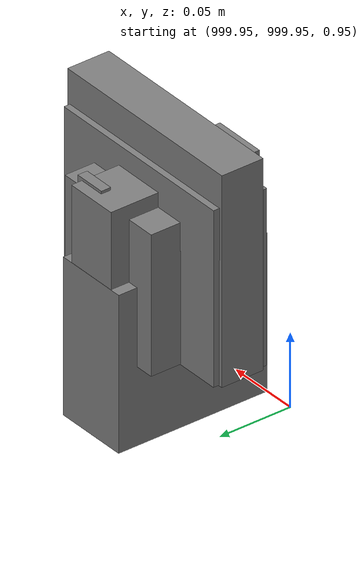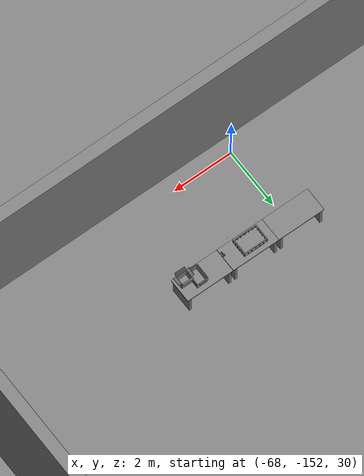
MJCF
<mujoco>
    <option gravity="0.000000000 0.000000000 -9.810000420" timestep="0.0049999999" integrator="implicitfast" density="1.225" viscosity="1.8000001e-05" noslip_iterations="10" iterations="100" sdf_iterations="50">
        <flag multiccd="disable"/>
    </option>
    <size memory="1000M"/>
    <compiler coordinate="local"/>
    <worldbody>
        <light cutoff="30" pos="0 1 1" dir="0 -1 -2"/>
        <light cutoff="30" pos="0 -1 1" dir="0 1 -2"/>
        <body pos="1000.000000000 1000.000000000 1.000000000" euler="0.000000000 0.000000000 180.000000000" name="openloong_gripper_2f85_fix_base_usda_battery_01">
            <geom contype="1" conaffinity="1" density="1000" type="box" material="" rgba="0.500000000 0.500000000 0.500000000 1.000000000" solimp="0.899999976 0.949999988 0.001000000" friction="1.000000000 0.005000000 0.000100000" solref="0.020000000 1.000000000" margin="0" condim="3" group="0" pos="-0.011123657 -0.041940309 0.101691343" quat="1.000000000 0.000000000 0.000000000 0.000000000" size="0.010800000 0.003375000 0.004725000" name="openloong_gripper_2f85_fix_base_usda_geom_B32E6A7E_2BBD_4091_A970_85A7B87EA5B8"/>
            <geom contype="1" conaffinity="1" density="1000" type="box" material="" rgba="0.500000000 0.500000000 0.500000000 1.000000000" solimp="0.899999976 0.949999988 0.001000000" friction="1.000000000 0.005000000 0.000100000" solref="0.020000000 1.000000000" margin="0" condim="3" group="0" pos="-0.010876465 -0.044247437 0.047066893" quat="0.998702705 -0.050920475 0.000000000 0.000000000" size="0.009450001 0.002700000 0.024975000" name="openloong_gripper_2f85_fix_base_usda_geom_66D66CAE_FBFC_4DA3_93E8_E0A731F0A1AA"/>
            <geom contype="1" conaffinity="1" density="1000" type="box" material="" rgba="0.500000000 0.500000000 0.500000000 1.000000000" solimp="0.899999976 0.949999988 0.001000000" friction="1.000000000 0.005000000 0.000100000" solref="0.020000000 1.000000000" margin="0" condim="3" group="0" pos="-0.001235962 -0.000659180 0.047381196" quat="1.000000000 0.000000000 0.000000000 0.000000000" size="0.039420001 0.039150000 0.047250003" name="openloong_gripper_2f85_fix_base_usda_geom_F7839ACB_6945_493D_AB74_1B866CE92D1F"/>
            <geom contype="1" conaffinity="1" density="1000" type="box" material="" rgba="0.500000000 0.500000000 0.500000000 1.000000000" solimp="0.899999976 0.949999988 0.001000000" friction="1.000000000 0.005000000 0.000100000" solref="0.020000000 1.000000000" margin="0" condim="3" group="0" pos="-0.010876465 -0.039138794 0.009851727" quat="1.000000000 0.000000000 0.000000000 0.000000000" size="0.009450001 0.010800000 0.013500000" name="openloong_gripper_2f85_fix_base_usda_geom_11F9241D_980D_4D36_A649_073F7A70F1C7"/>
            <geom contype="1" conaffinity="1" density="1000" type="box" material="" rgba="0.500000000 0.500000000 0.500000000 1.000000000" solimp="0.899999976 0.949999988 0.001000000" friction="1.000000000 0.005000000 0.000100000" solref="0.020000000 1.000000000" margin="0" condim="3" group="0" pos="-0.010876465 -0.041528322 0.071508206" quat="1.000000000 0.000000000 0.000000000 0.000000000" size="0.009450001 0.002700000 0.027000001" name="openloong_gripper_2f85_fix_base_usda_geom_CC7DCD5B_A1AE_42D7_BD8F_D8EE2A39102D"/>
            <freejoint name="openloong_gripper_2f85_fix_base_usda_battery_01_joint"/>
            <site size="0.005000000 0.005000000 0.005000000" rgba="0.500000000 0.500000000 0.500000000 1.000000000" pos="0.000000000 0.000000000 0.000000000" quat="0.999961913 0.008726500 0.000000000 0.000000000" group="0" type="sphere" name="openloong_gripper_2f85_fix_base_usda_battery_01site"/>
        </body>
        <body pos="1000.000000000 1000.000000000 1.000000000" euler="0.000000000 0.000000000 180.000000000" name="openloong_gripper_2f85_fix_base_usda_cpu_fan">
            <geom contype="1" conaffinity="1" density="1000" type="box" material="" rgba="0.500000000 0.500000000 0.500000000 1.000000000" solimp="0.899999976 0.949999988 0.001000000" friction="1.000000000 0.005000000 0.000100000" solref="0.020000000 1.000000000" margin="0" condim="3" group="0" pos="0.000000000 0.000000000 0.070034981" quat="0.000000000 0.000000000 0.000000000 1.000000000" size="0.070700005 0.014699999 0.070700005" name="openloong_gripper_2f85_fix_base_usda_geom_63BFF26A_E785_4080_A1AF_E1921EC5DF24"/>
            <freejoint name="openloong_gripper_2f85_fix_base_usda_cpu_fan_joint"/>
            <site size="0.005000000 0.005000000 0.005000000" rgba="0.500000000 0.500000000 0.500000000 1.000000000" pos="0.000000000 0.000000000 0.000000000" quat="0.999961913 0.008726535 0.000000000 0.000000000" group="0" type="sphere" name="openloong_gripper_2f85_fix_base_usda_cpu_fancsite"/>
        </body>
        <body pos="1000.000000000 1000.000000000 1.000000000" euler="0.000000000 0.000000000 180.000000000" name="openloong_gripper_2f85_fix_base_usda_wifi_box">
            <geom contype="1" conaffinity="1" density="1000" type="box" material="" rgba="0.500000000 0.500000000 0.500000000 1.000000000" solimp="0.899999976 0.949999988 0.001000000" friction="1.000000000 0.005000000 0.000100000" solref="0.020000000 1.000000000" margin="0" condim="3" group="0" pos="0.000000000 0.000000000 0.058978677" quat="0.000000000 0.000000047 0.000000000 1.000000000" size="0.068499997 0.018999999 0.059000000" name="openloong_gripper_2f85_fix_base_usda_geom_BFF527B0_2CD7_4A62_A344_B4BCD9A0947D"/>
            <freejoint name="openloong_gripper_2f85_fix_base_usda_wifi_box_joint"/>
            <site size="0.005000000 0.005000000 0.005000000" rgba="0.500000000 0.500000000 0.500000000 1.000000000" pos="0.000000000 0.000000000 0.000000000" quat="0.999961913 0.008726500 0.000000000 0.000000000" group="0" type="sphere" name="openloong_gripper_2f85_fix_base_usda_wifi_boxsite"/>
        </body>
        <body pos="-66.250717163 -148.917022705 31.169691086" euler="-160.394027710 -27.502695084 -116.779029846" mocap="true" name="spotlight6_SpotLight"/>
        <body pos="1000.000000000 1000.000000000 1.000000000" euler="0.000011953 0.000005123 -179.999984741" name="openloong_gripper_2f85_fix_base_usda_intel_box">
            <geom contype="1" conaffinity="1" density="1000" type="box" material="" rgba="0.500000000 0.500000000 0.500000000 1.000000000" solimp="0.899999976 0.949999988 0.001000000" friction="1.000000000 0.005000000 0.000100000" solref="0.020000000 1.000000000" margin="0" condim="3" group="0" pos="0.000000000 -0.000067139 0.000082284" quat="0.707106709 0.000000225 0.000000253 0.707106650" size="0.052800003 0.025300000 0.052800003" name="openloong_gripper_2f85_fix_base_usda_geom_10DD114A_39EF_40C3_A82E_24F57155389E"/>
            <freejoint name="openloong_gripper_2f85_fix_base_usda_intel_box_joint"/>
            <site size="0.005000000 0.005000000 0.005000000" rgba="0.500000000 0.500000000 0.500000000 1.000000000" pos="0.000000000 0.000000000 0.000000000" quat="0.999961913 0.008726500 0.000000000 0.000000000" group="0" type="sphere" name="openloong_gripper_2f85_fix_base_usda_intel_boxsite"/>
        </body>
        <body pos="1000.000000000 999.999938965 1.000000000" euler="0.000000000 0.000000000 180.000000000" name="openloong_gripper_2f85_fix_base_usda_intelcore_i5">
            <geom contype="1" conaffinity="1" density="1000" type="box" material="" rgba="0.500000000 0.500000000 0.500000000 1.000000000" solimp="0.899999976 0.949999988 0.001000000" friction="1.000000000 0.005000000 0.000100000" solref="0.020000000 1.000000000" margin="0" condim="3" group="0" pos="0.000000000 0.000000000 0.051722717" quat="0.707106709 0.000000000 0.000000000 -0.707106769" size="0.052800000 0.018080002 0.052800000" name="openloong_gripper_2f85_fix_base_usda_geom_C7D06C12_A7FC_4E84_A35B_83860271027F"/>
            <freejoint name="openloong_gripper_2f85_fix_base_usda_intelcore_i5_joint"/>
            <site size="0.005000000 0.005000000 0.005000000" rgba="0.500000000 0.500000000 0.500000000 1.000000000" pos="0.000000000 0.000000000 0.000000000" quat="0.999961913 0.008726534 0.000000000 0.000000000" group="0" type="sphere" name="openloong_gripper_2f85_fix_base_usda_intelcore_i5site"/>
        </body>
        <body pos="-65.954162598 -149.753616333 31.171535492" euler="-28.898550034 -0.806787372 -177.846389771" mocap="true" name="spotlight2_SpotLight"/>
        <body pos="-66.221130371 -148.965637207 31.167303085" euler="132.551818848 -15.696949005 21.368698120" mocap="true" name="spotlight1_SpotLight"/>
        <body pos="-64.866622925 -149.383972168 30.183746338" euler="89.999984741 89.999946594 0.000000000" name="openloong_gripper_2f85_fix_base_usda_bluebox_01">
            <geom contype="1" conaffinity="1" density="1000" type="box" material="" rgba="0.500000000 0.500000000 0.500000000 1.000000000" solimp="0.899999976 0.949999988 0.001000000" friction="1.000000000 0.005000000 0.000100000" solref="0.020000000 1.000000000" margin="0" condim="3" group="0" pos="0.276580811 0.187225342 0.000068665" quat="0.707106948 0.000077471 0.707106352 0.000077486" size="0.100000001 0.057999998 0.010000000" name="openloong_gripper_2f85_fix_base_usda_geom_B8B5E5F3_B8DC_42CF_974D_72148CB7F6BE"/>
            <geom contype="1" conaffinity="1" density="1000" type="box" material="" rgba="0.500000000 0.500000000 0.500000000 1.000000000" solimp="0.899999976 0.949999988 0.001000000" friction="1.000000000 0.005000000 0.000100000" solref="0.020000000 1.000000000" margin="0" condim="3" group="0" pos="0.000000000 0.002883911 0.000000000" quat="0.999999881 0.000000000 0.000000000 0.000000000" size="0.254000008 0.003000000 0.172000006" name="openloong_gripper_2f85_fix_base_usda_geom_CDAD1561_C436_4F5F_B8E2_BD874B268317"/>
            <geom contype="1" conaffinity="1" density="1000" type="box" material="" rgba="0.500000000 0.500000000 0.500000000 1.000000000" solimp="0.899999976 0.949999988 0.001000000" friction="1.000000000 0.005000000 0.000100000" solref="0.020000000 1.000000000" margin="0" condim="3" group="0" pos="0.000000000 0.124874115 0.173484802" quat="0.999796331 0.020176515 -0.000000015 0.000000030" size="0.259999990 0.119999997 0.007000000" name="openloong_gripper_2f85_fix_base_usda_geom_9DF58FB6_D7A2_47BF_932D_3FD9AB4ECFFA"/>
            <geom contype="1" conaffinity="1" density="1000" type="box" material="" rgba="0.500000000 0.500000000 0.500000000 1.000000000" solimp="0.899999976 0.949999988 0.001000000" friction="1.000000000 0.005000000 0.000100000" solref="0.020000000 1.000000000" margin="0" condim="3" group="0" pos="0.000000000 0.124874115 -0.173469543" quat="0.999796331 -0.020176545 -0.000000015 0.000000000" size="0.259999990 0.119999997 0.007000000" name="openloong_gripper_2f85_fix_base_usda_geom_199E8DBC_0BB3_4D48_96B8_3B25B6941033"/>
            <geom contype="1" conaffinity="1" density="1000" type="box" material="" rgba="0.500000000 0.500000000 0.500000000 1.000000000" solimp="0.899999976 0.949999988 0.001000000" friction="1.000000000 0.005000000 0.000100000" solref="0.020000000 1.000000000" margin="0" condim="3" group="0" pos="0.000000000 0.214008331 0.188980103" quat="0.999912977 0.013176724 0.000000015 0.000000000" size="0.259999990 0.029999999 0.012500000" name="openloong_gripper_2f85_fix_base_usda_geom_F6FE680E_AA25_4E25_A33A_BA0CB4D2BCCB"/>
            <geom contype="1" conaffinity="1" density="1000" type="box" material="" rgba="0.500000000 0.500000000 0.500000000 1.000000000" solimp="0.899999976 0.949999988 0.001000000" friction="1.000000000 0.005000000 0.000100000" solref="0.020000000 1.000000000" margin="0" condim="3" group="0" pos="-0.258361816 0.125289917 0.001876831" quat="0.702796936 -0.020792112 0.710783124 0.020769298" size="0.189999998 0.119999997 0.009000000" name="openloong_gripper_2f85_fix_base_usda_geom_2870BF18_9E3E_457D_BF8D_D9D40296E281"/>
            <geom contype="1" conaffinity="1" density="1000" type="box" material="" rgba="0.500000000 0.500000000 0.500000000 1.000000000" solimp="0.899999976 0.949999988 0.001000000" friction="1.000000000 0.005000000 0.000100000" solref="0.020000000 1.000000000" margin="0" condim="3" group="0" pos="0.000000000 0.214008331 -0.188980103" quat="0.999912977 -0.013176769 0.000000030 0.000000015" size="0.259999990 0.029999999 0.012500000" name="openloong_gripper_2f85_fix_base_usda_geom_6ED9C6CC_919A_463D_8606_52AEDD7A0734"/>
            <geom contype="1" conaffinity="1" density="1000" type="box" material="" rgba="0.500000000 0.500000000 0.500000000 1.000000000" solimp="0.899999976 0.949999988 0.001000000" friction="1.000000000 0.005000000 0.000100000" solref="0.020000000 1.000000000" margin="0" condim="3" group="0" pos="-0.276611328 0.187225342 0.000068665" quat="0.707106650 0.000077441 0.707106709 0.000077456" size="0.100000001 0.057999998 0.010000000" name="openloong_gripper_2f85_fix_base_usda_geom_AC561AAD_1161_4D44_BBC2_2FC8C89BD4E4"/>
            <geom contype="1" conaffinity="1" density="1000" type="box" material="" rgba="0.500000000 0.500000000 0.500000000 1.000000000" solimp="0.899999976 0.949999988 0.001000000" friction="1.000000000 0.005000000 0.000100000" solref="0.020000000 1.000000000" margin="0" condim="3" group="0" pos="0.258331299 0.125289917 0.001876831" quat="0.702851415 0.018856421 0.710823774 -0.019329369" size="0.189999998 0.119999997 0.009000000" name="openloong_gripper_2f85_fix_base_usda_geom_983C9DDD_F565_4DB2_AAC4_2B8F9AC420D3"/>
            <freejoint name="openloong_gripper_2f85_fix_base_usda_bluebox_01_joint"/>
            <site size="0.005000000 0.005000000 0.005000000" rgba="0.500000000 0.500000000 0.500000000 1.000000000" pos="0.000000000 0.000000000 0.000000000" quat="0.999961913 0.008726534 0.000000000 0.000000000" group="0" type="sphere" name="openloong_gripper_2f85_fix_base_usda_bluebox_01site"/>
        </body>
        <body pos="-64.496299744 -149.491867065 30.235729218" euler="0.000000000 0.000000000 89.999946594" name="openloong_gripper_2f85_fix_base_usda_cardboardbox_01">
            <geom contype="1" conaffinity="1" density="1000" type="box" material="" rgba="0.500000000 0.500000000 0.500000000 1.000000000" solimp="0.899999976 0.949999988 0.001000000" friction="1.000000000 0.005000000 0.000100000" solref="0.020000000 1.000000000" margin="0" condim="3" group="0" pos="-0.003166199 -0.004086494 0.005052090" quat="1.000000000 0.000000000 0.000000000 0.000000000" size="0.142499998 0.177500010 0.005000000" name="openloong_gripper_2f85_fix_base_usda_geom_E0950F45_79E3_4C85_BBF7_63919E8099F4"/>
            <geom contype="1" conaffinity="1" density="1000" type="box" material="" rgba="0.500000000 0.500000000 0.500000000 1.000000000" solimp="0.899999976 0.949999988 0.001000000" friction="1.000000000 0.005000000 0.000100000" solref="0.020000000 1.000000000" margin="0" condim="3" group="0" pos="-0.003166199 0.170316696 0.150570869" quat="1.000000000 0.000000000 0.000000000 0.000000000" size="0.142499998 0.005000000 0.149999991" name="openloong_gripper_2f85_fix_base_usda_geom_F0804FB5_A778_4E6B_9F8B_61E85B480A25"/>
            <geom contype="1" conaffinity="1" density="1000" type="box" material="" rgba="0.500000000 0.500000000 0.500000000 1.000000000" solimp="0.899999976 0.949999988 0.001000000" friction="1.000000000 0.005000000 0.000100000" solref="0.020000000 1.000000000" margin="0" condim="3" group="0" pos="-0.147399902 -0.005307198 0.150570869" quat="1.000000000 0.000000000 0.000000000 0.000000000" size="0.005000000 0.177500010 0.149999991" name="openloong_gripper_2f85_fix_base_usda_geom_5F1B6B1D_4AD2_4075_A2DA_754C8E056740"/>
            <geom contype="1" conaffinity="1" density="1000" type="box" material="" rgba="0.500000000 0.500000000 0.500000000 1.000000000" solimp="0.899999976 0.949999988 0.001000000" friction="1.000000000 0.005000000 0.000100000" solref="0.020000000 1.000000000" margin="0" condim="3" group="0" pos="0.140275955 -0.005307198 0.150570869" quat="1.000000000 0.000000000 0.000000000 0.000000000" size="0.005000000 0.177500010 0.149999991" name="openloong_gripper_2f85_fix_base_usda_geom_21534D9A_30E5_4F38_8211_6600B221AC88"/>
            <geom contype="1" conaffinity="1" density="1000" type="box" material="" rgba="0.500000000 0.500000000 0.500000000 1.000000000" solimp="0.899999976 0.949999988 0.001000000" friction="1.000000000 0.005000000 0.000100000" solref="0.020000000 1.000000000" margin="0" condim="3" group="0" pos="-0.003166199 -0.181550980 0.150570869" quat="1.000000000 0.000000000 0.000000000 0.000000000" size="0.142499998 0.005000000 0.149999991" name="openloong_gripper_2f85_fix_base_usda_geom_DDB4E63C_75D8_4D01_98BE_A08B094FBC0A"/>
            <freejoint name="openloong_gripper_2f85_fix_base_usda_cardboardbox_01_joint"/>
            <site size="0.005000000 0.005000000 0.005000000" rgba="0.500000000 0.500000000 0.500000000 1.000000000" pos="0.000000000 0.000000000 0.000000000" quat="0.999961913 0.008726535 0.000000000 0.000000000" group="0" type="sphere" name="openloong_gripper_2f85_fix_base_usda_site_088051B8_FB41_4A2D_ACFF_27E5C0C30A83"/>
            <body pos="0.139160156 -0.004048347 0.301930904" euler="-179.999954224 49.383502960 179.999954224" name="openloong_gripper_2f85_fix_base_usda_A1_006">
                <geom contype="1" conaffinity="1" density="1000" type="box" material="" rgba="0.500000000 0.500000000 0.500000000 1.000000000" solimp="0.899999976 0.949999988 0.001000000" friction="1.000000000 0.005000000 0.000100000" solref="0.020000000 1.000000000" margin="0" condim="3" group="0" pos="-0.071587563 0.000009537 0.001745224" quat="0.999999881 0.000000000 0.000000000 0.000000000" size="0.071249999 0.179999992 0.002500000" name="openloong_gripper_2f85_fix_base_usda_geom_C04A047B_291F_4F61_A8C1_9A0033D482D6"/>
                <joint armature="0" stiffness="0.07" damping="0.0099999998" axis="0.000000 1.000000 0.000000" type="hinge" name="openloong_gripper_2f85_fix_base_usda_A1_006"/>
            </body>
            <body pos="-0.145902634 -0.004086494 0.301938057" euler="-180.000000000 -60.000011444 -180.000000000" name="openloong_gripper_2f85_fix_base_usda_A2_006">
                <geom contype="1" conaffinity="1" density="1000" type="box" material="" rgba="0.500000000 0.500000000 0.500000000 1.000000000" solimp="0.899999976 0.949999988 0.001000000" friction="1.000000000 0.005000000 0.000100000" solref="0.020000000 1.000000000" margin="0" condim="3" group="0" pos="0.071268082 0.000009537 0.002717972" quat="0.000002921 0.000000000 -0.000000030 0.999999881" size="0.071249999 0.179999992 0.002500000" name="openloong_gripper_2f85_fix_base_usda_geom_BB78E120_E8F8_49DD_9C81_15C634680FA9"/>
                <joint armature="0" stiffness="0.07" damping="0.0099999998" axis="0.000000 1.000000 0.000000" type="hinge" name="openloong_gripper_2f85_fix_base_usda_A2_006"/>
            </body>
            <body pos="-0.003385544 0.175991058 0.301930904" euler="-125.858116150 -0.000004561 0.000002331" name="openloong_gripper_2f85_fix_base_usda_B2_006">
                <geom contype="1" conaffinity="1" density="1000" type="box" material="" rgba="0.500000000 0.500000000 0.500000000 1.000000000" solimp="0.899999976 0.949999988 0.001000000" friction="1.000000000 0.005000000 0.000100000" solref="0.020000000 1.000000000" margin="0" condim="3" group="0" pos="0.000009537 -0.070939064 -0.002470016" quat="0.999614120 0.027776197 -0.000000015 0.000000030" size="0.137500003 0.064999998 0.005000000" name="openloong_gripper_2f85_fix_base_usda_geom_DA179B54_E914_498C_9B37_EDEB419AC484"/>
                <joint armature="0" stiffness="0.07" damping="0.0099999998" axis="1.000000 0.000000 0.000000" type="hinge" name="openloong_gripper_2f85_fix_base_usda_B2_006"/>
            </body>
            <body pos="-0.003385544 -0.184140205 0.301938057" euler="147.805557251 0.000000000 0.000000000" name="openloong_gripper_2f85_fix_base_usda_B1_006">
                <geom contype="1" conaffinity="1" density="1000" type="box" material="" rgba="0.500000000 0.500000000 0.500000000 1.000000000" solimp="0.899999976 0.949999988 0.001000000" friction="1.000000000 0.005000000 0.000100000" solref="0.020000000 1.000000000" margin="0" condim="3" group="0" pos="-0.000028610 0.070202351 -0.002703667" quat="0.999614179 -0.027776167 0.000000000 0.000000000" size="0.137500003 0.064999998 0.005000000" name="openloong_gripper_2f85_fix_base_usda_geom_B0EB9C13_FB89_4F59_B4C0_90A8583BA0AB"/>
                <joint armature="0" stiffness="0.07" damping="0.0099999998" axis="1.000000 0.000000 0.000000" type="hinge" name="openloong_gripper_2f85_fix_base_usda_B1_006"/>
            </body>
        </body>
        <body pos="-65.882858276 -149.481979370 30.229999542" euler="-64.487716675 0.000000000 0.000000000" name="openloong_gripper_2f85_fix_base_usda_Barcode">
            <geom contype="1" conaffinity="1" density="1000" type="box" material="" rgba="0.500000000 0.500000000 0.500000000 1.000000000" solimp="0.899999976 0.949999988 0.001000000" friction="1.000000000 0.005000000 0.000100000" solref="0.020000000 1.000000000" margin="0" condim="3" group="0" pos="0.000000000 0.013038635 0.001419067" quat="0.000000000 0.000000000 0.000000000 1.000000119" size="0.034000002 0.010000000 0.017999999" name="openloong_gripper_2f85_fix_base_usda_geom_1D01C158_CDAD_4481_854B_5869DEAE1A3D"/>
            <geom contype="1" conaffinity="1" density="1000" type="box" material="" rgba="0.500000000 0.500000000 0.500000000 1.000000000" solimp="0.899999976 0.949999988 0.001000000" friction="1.000000000 0.005000000 0.000100000" solref="0.020000000 1.000000000" margin="0" condim="3" group="0" pos="0.000000000 -0.035301208 -0.007095337" quat="0.000000000 0.000000000 -0.043619365 0.999048233" size="0.028999999 0.010000000 0.020000000" name="openloong_gripper_2f85_fix_base_usda_geom_1453B713_2DBE_48C4_B756_999B1C2A2730"/>
            <geom contype="1" conaffinity="1" density="1000" type="box" material="" rgba="0.500000000 0.500000000 0.500000000 1.000000000" solimp="0.899999976 0.949999988 0.001000000" friction="1.000000000 0.005000000 0.000100000" solref="0.020000000 1.000000000" margin="0" condim="3" group="0" pos="0.000000000 -0.043411255 -0.011749268" quat="0.922262907 0.386563420 0.000000000 0.000000000" size="0.026000001 0.010000000 0.020000000" name="openloong_gripper_2f85_fix_base_usda_geom_C50F4A63_BA60_4B8B_945C_D16801EF8953"/>
            <geom contype="1" conaffinity="1" density="1000" type="box" material="" rgba="0.500000000 0.500000000 0.500000000 1.000000000" solimp="0.899999976 0.949999988 0.001000000" friction="1.000000000 0.005000000 0.000100000" solref="0.020000000 1.000000000" margin="0" condim="3" group="0" pos="0.000000000 -0.016967773 -0.031860352" quat="0.000000000 0.000000000 0.000000000 1.000000119" size="0.008000000 0.010000000 0.013000000" name="openloong_gripper_2f85_fix_base_usda_geom_A8853594_D3CD_4923_8518_2971B343B2D8"/>
            <geom contype="1" conaffinity="1" density="1000" type="box" material="" rgba="0.500000000 0.500000000 0.500000000 1.000000000" solimp="0.899999976 0.949999988 0.001000000" friction="1.000000000 0.005000000 0.000100000" solref="0.020000000 1.000000000" margin="0" condim="3" group="0" pos="0.000000000 -0.001869202 0.000312805" quat="0.953716993 0.300705761 0.000000000 0.000000000" size="0.032000002 0.010000000 0.018999999" name="openloong_gripper_2f85_fix_base_usda_geom_1AA7E267_225F_4017_AA9B_33637D1664B3"/>
            <geom contype="1" conaffinity="1" density="1000" type="box" material="" rgba="0.500000000 0.500000000 0.500000000 1.000000000" solimp="0.899999976 0.949999988 0.001000000" friction="1.000000000 0.005000000 0.000100000" solref="0.020000000 1.000000000" margin="0" condim="3" group="0" pos="0.000000000 -0.019531250 -0.003173828" quat="0.953716993 0.300705761 0.000000000 0.000000000" size="0.030999999 0.010000000 0.020000000" name="openloong_gripper_2f85_fix_base_usda_geom_DD82EA6E_1B68_479B_870D_DA4F17F5AE65"/>
            <geom contype="1" conaffinity="1" density="1000" type="box" material="" rgba="0.500000000 0.500000000 0.500000000 1.000000000" solimp="0.899999976 0.949999988 0.001000000" friction="1.000000000 0.005000000 0.000100000" solref="0.020000000 1.000000000" margin="0" condim="3" group="0" pos="0.000000000 -0.035301208 -0.007095337" quat="0.953716993 0.300705761 0.000000000 0.000000000" size="0.028999999 0.010000000 0.020000000" name="openloong_gripper_2f85_fix_base_usda_geom_F8FAF0D8_575F_4D69_9A4E_641BB6432906"/>
            <geom contype="1" conaffinity="1" density="1000" type="box" material="" rgba="0.500000000 0.500000000 0.500000000 1.000000000" solimp="0.899999976 0.949999988 0.001000000" friction="1.000000000 0.005000000 0.000100000" solref="0.020000000 1.000000000" margin="0" condim="3" group="0" pos="0.000000000 -0.042617798 -0.071121216" quat="0.000000000 0.000000000 0.000000000 1.000000119" size="0.013000000 0.021000000 0.059999999" name="openloong_gripper_2f85_fix_base_usda_geom_219387BC_FC7F_4889_9D2C_EEB54B6D569F"/>
            <freejoint name="openloong_gripper_2f85_fix_base_usda_Barcode_joint"/>
            <site size="0.005000000 0.005000000 0.005000000" rgba="0.500000000 0.500000000 0.500000000 1.000000000" pos="0.000000000 0.000000000 0.000000000" quat="1.000000000 0.000000000 0.000000000 0.000000000" group="0" type="sphere" name="openloong_gripper_2f85_fix_base_usda_Barcode_site"/>
        </body>
        <body pos="-66.745018005 -149.392349243 30.184000015" euler="0.000000000 0.000000000 89.999946594" name="[22333641089939]_Basket_01">
            <geom contype="1" conaffinity="1" density="1000" type="box" material="" rgba="0.500000000 0.500000000 0.500000000 1.000000000" solimp="0.899999976 0.949999988 0.001000000" friction="1.000000000 0.005000000 0.000100000" solref="0.020000000 1.000000000" margin="0" condim="3" group="0" pos="-0.052425385 0.389207840 0.089787483" quat="0.707107008 0.000000000 0.000000000 0.707106411" size="0.014249999 0.014249999 0.059999999" name="[22333641089939]_geom_86F1581B_E77B_4F82_8375_1A1D0B1A2F39"/>
            <geom contype="1" conaffinity="1" density="1000" type="box" material="" rgba="0.500000000 0.500000000 0.500000000 1.000000000" solimp="0.899999976 0.949999988 0.001000000" friction="1.000000000 0.005000000 0.000100000" solref="0.020000000 1.000000000" margin="0" condim="3" group="0" pos="0.264015198 -0.133043289 0.089787483" quat="0.707107008 0.000000000 0.000000000 0.707106411" size="0.014249999 0.014249999 0.059999999" name="[22333641089939]_geom_A71FCC38_D665_43F9_B451_BC5EFC97DF1E"/>
            <geom contype="1" conaffinity="1" density="1000" type="box" material="" rgba="0.500000000 0.500000000 0.500000000 1.000000000" solimp="0.899999976 0.949999988 0.001000000" friction="1.000000000 0.005000000 0.000100000" solref="0.020000000 1.000000000" margin="0" condim="3" group="0" pos="-0.264015198 -0.265548706 0.089793205" quat="0.707107008 0.000000000 0.000000000 0.707106411" size="0.014249999 0.014249999 0.059999999" name="[22333641089939]_geom_4C765A36_FDA6_46C3_9BDB_2D17DA8AA561"/>
            <geom contype="1" conaffinity="1" density="1000" type="box" material="" rgba="0.500000000 0.500000000 0.500000000 1.000000000" solimp="0.899999976 0.949999988 0.001000000" friction="1.000000000 0.005000000 0.000100000" solref="0.020000000 1.000000000" margin="0" condim="3" group="0" pos="-0.160263062 -0.389322281 0.089793205" quat="0.707107008 0.000000000 0.000000000 0.707106411" size="0.014249999 0.014249999 0.059999999" name="[22333641089939]_geom_76E91671_D6D3_45F8_9028_896B98F735A9"/>
            <geom contype="1" conaffinity="1" density="1000" type="box" material="" rgba="0.500000000 0.500000000 0.500000000 1.000000000" solimp="0.899999976 0.949999988 0.001000000" friction="1.000000000 0.005000000 0.000100000" solref="0.020000000 1.000000000" margin="0" condim="3" group="0" pos="0.162265778 -0.389322281 0.089787483" quat="0.707107008 0.000000000 0.000000000 0.707106411" size="0.014249999 0.014249999 0.059999999" name="[22333641089939]_geom_3B19A87B_945F_4E66_9D5E_A07BEE922A42"/>
            <geom contype="1" conaffinity="1" density="1000" type="box" material="" rgba="0.500000000 0.500000000 0.500000000 1.000000000" solimp="0.899999976 0.949999988 0.001000000" friction="1.000000000 0.005000000 0.000100000" solref="0.020000000 1.000000000" margin="0" condim="3" group="0" pos="0.264015198 0.389207840 0.089787483" quat="0.707107008 0.000000000 0.000000000 0.707106411" size="0.014249999 0.014249999 0.059999999" name="[22333641089939]_geom_6F3C2C2D_469C_4B4B_B89D_74DAC6697C11"/>
            <geom contype="1" conaffinity="1" density="1000" type="box" material="" rgba="0.500000000 0.500000000 0.500000000 1.000000000" solimp="0.899999976 0.949999988 0.001000000" friction="1.000000000 0.005000000 0.000100000" solref="0.020000000 1.000000000" margin="0" condim="3" group="0" pos="-0.264015198 -0.133043289 0.089793205" quat="0.707107008 0.000000000 0.000000000 0.707106411" size="0.014249999 0.014249999 0.059999999" name="[22333641089939]_geom_B51587F4_0378_4509_B65F_7EE773761FEF"/>
            <geom contype="1" conaffinity="1" density="1000" type="box" material="" rgba="0.500000000 0.500000000 0.500000000 1.000000000" solimp="0.899999976 0.949999988 0.001000000" friction="1.000000000 0.005000000 0.000100000" solref="0.020000000 1.000000000" margin="0" condim="3" group="0" pos="-0.264026642 0.269256592 0.089793205" quat="0.707107008 0.000000000 0.000000000 0.707106411" size="0.014249999 0.014249999 0.059999999" name="[22333641089939]_geom_94DB84A0_6749_44D3_8501_E7AFBD3B64A4"/>
            <geom contype="1" conaffinity="1" density="1000" type="box" material="" rgba="0.500000000 0.500000000 0.500000000 1.000000000" solimp="0.899999976 0.949999988 0.001000000" friction="1.000000000 0.005000000 0.000100000" solref="0.020000000 1.000000000" margin="0" condim="3" group="0" pos="0.054462433 0.389207840 0.089787483" quat="0.707107008 0.000000000 0.000000000 0.707106411" size="0.014249999 0.014249999 0.059999999" name="[22333641089939]_geom_E2C6EAF3_A626_492F_B5E4_6305E68B69E2"/>
            <geom contype="1" conaffinity="1" density="1000" type="box" material="" rgba="0.500000000 0.500000000 0.500000000 1.000000000" solimp="0.899999976 0.949999988 0.001000000" friction="1.000000000 0.005000000 0.000100000" solref="0.020000000 1.000000000" margin="0" condim="3" group="0" pos="0.054462433 -0.389322281 0.089787483" quat="0.707107008 0.000000000 0.000000000 0.707106411" size="0.014249999 0.014249999 0.059999999" name="[22333641089939]_geom_C36CD9C0_1FFB_4116_AACF_B0B6D9EE40DB"/>
            <geom contype="1" conaffinity="1" density="1000" type="box" material="" rgba="0.500000000 0.500000000 0.500000000 1.000000000" solimp="0.899999976 0.949999988 0.001000000" friction="1.000000000 0.005000000 0.000100000" solref="0.020000000 1.000000000" margin="0" condim="3" group="0" pos="0.264015198 0.269256592 0.089793205" quat="0.707107008 0.000000000 0.000000000 0.707106411" size="0.014249999 0.014249999 0.059999999" name="[22333641089939]_geom_EB6C012A_5C89_4637_ADD3_5ED1A668493E"/>
            <geom contype="1" conaffinity="1" density="1000" type="box" material="" rgba="0.500000000 0.500000000 0.500000000 1.000000000" solimp="0.899999976 0.949999988 0.001000000" friction="1.000000000 0.005000000 0.000100000" solref="0.020000000 1.000000000" margin="0" condim="3" group="0" pos="0.264015198 -0.389322281 0.089787483" quat="0.707107008 0.000000000 0.000000000 0.707106411" size="0.014249999 0.014249999 0.059999999" name="[22333641089939]_geom_A62B014C_E0A8_49F0_BC80_87BA51294962"/>
            <geom contype="1" conaffinity="1" density="1000" type="box" material="" rgba="0.500000000 0.500000000 0.500000000 1.000000000" solimp="0.899999976 0.949999988 0.001000000" friction="1.000000000 0.005000000 0.000100000" solref="0.020000000 1.000000000" margin="0" condim="3" group="0" pos="0.000000000 0.000000000 0.015998840" quat="0.707107008 0.000000000 0.000000000 0.707106411" size="0.403499991 0.279000014 0.015750000" name="[22333641089939]_geom_C23278E7_983D_46DB_A8B0_57D9F435FDA7"/>
            <geom contype="1" conaffinity="1" density="1000" type="box" material="" rgba="0.500000000 0.500000000 0.500000000 1.000000000" solimp="0.899999976 0.949999988 0.001000000" friction="1.000000000 0.005000000 0.000100000" solref="0.020000000 1.000000000" margin="0" condim="3" group="0" pos="0.000000000 -0.389476776 0.163619041" quat="0.707107008 0.000000000 0.000000000 0.707106411" size="0.015000000 0.277500004 0.015750000" name="[22333641089939]_geom_31BCCCB6_88B9_426C_9DCB_DFDE63C2BAD7"/>
            <geom contype="1" conaffinity="1" density="1000" type="box" material="" rgba="0.500000000 0.500000000 0.500000000 1.000000000" solimp="0.899999976 0.949999988 0.001000000" friction="1.000000000 0.005000000 0.000100000" solref="0.020000000 1.000000000" margin="0" condim="3" group="0" pos="0.162265778 0.389207840 0.089787483" quat="0.707107008 0.000000000 0.000000000 0.707106411" size="0.014249999 0.014249999 0.059999999" name="[22333641089939]_geom_A57083E3_7C44_46BE_A53F_142AB48D1453"/>
            <geom contype="1" conaffinity="1" density="1000" type="box" material="" rgba="0.500000000 0.500000000 0.500000000 1.000000000" solimp="0.899999976 0.949999988 0.001000000" friction="1.000000000 0.005000000 0.000100000" solref="0.020000000 1.000000000" margin="0" condim="3" group="0" pos="0.000000000 0.389471054 0.163619041" quat="0.707107008 0.000000000 0.000000000 0.707106411" size="0.015000000 0.277500004 0.015750000" name="[22333641089939]_geom_74E5A7F6_1CD0_441A_BF20_84A88395300E"/>
            <geom contype="1" conaffinity="1" density="1000" type="box" material="" rgba="0.500000000 0.500000000 0.500000000 1.000000000" solimp="0.899999976 0.949999988 0.001000000" friction="1.000000000 0.005000000 0.000100000" solref="0.020000000 1.000000000" margin="0" condim="3" group="0" pos="-0.263511658 0.000000000 0.163619041" quat="0.707107008 0.000000000 0.000000000 0.707106411" size="0.403499991 0.015000000 0.015750000" name="[22333641089939]_geom_A4AE9194_96B5_4091_8010_16069137DFFA"/>
            <geom contype="1" conaffinity="1" density="1000" type="box" material="" rgba="0.500000000 0.500000000 0.500000000 1.000000000" solimp="0.899999976 0.949999988 0.001000000" friction="1.000000000 0.005000000 0.000100000" solref="0.020000000 1.000000000" margin="0" condim="3" group="0" pos="-0.264015198 0.141334534 0.089793205" quat="0.707107008 0.000000000 0.000000000 0.707106411" size="0.014249999 0.014249999 0.059999999" name="[22333641089939]_geom_AF81D20C_1023_4760_B51F_A542E046993B"/>
            <geom contype="1" conaffinity="1" density="1000" type="box" material="" rgba="0.500000000 0.500000000 0.500000000 1.000000000" solimp="0.899999976 0.949999988 0.001000000" friction="1.000000000 0.005000000 0.000100000" solref="0.020000000 1.000000000" margin="0" condim="3" group="0" pos="0.264015198 -0.265548706 0.089787483" quat="0.707107008 0.000000000 0.000000000 0.707106411" size="0.014249999 0.014249999 0.059999999" name="[22333641089939]_geom_626BEBDB_DD69_420C_9019_4E04AA61558B"/>
            <geom contype="1" conaffinity="1" density="1000" type="box" material="" rgba="0.500000000 0.500000000 0.500000000 1.000000000" solimp="0.899999976 0.949999988 0.001000000" friction="1.000000000 0.005000000 0.000100000" solref="0.020000000 1.000000000" margin="0" condim="3" group="0" pos="-0.160263062 0.389207840 0.089787483" quat="0.707107008 0.000000000 0.000000000 0.707106411" size="0.014249999 0.014249999 0.059999999" name="[22333641089939]_geom_59ED5C78_EB32_4032_B54B_99689BBDE07A"/>
            <geom contype="1" conaffinity="1" density="1000" type="box" material="" rgba="0.500000000 0.500000000 0.500000000 1.000000000" solimp="0.899999976 0.949999988 0.001000000" friction="1.000000000 0.005000000 0.000100000" solref="0.020000000 1.000000000" margin="0" condim="3" group="0" pos="-0.052425385 -0.389322281 0.089787483" quat="0.707107008 0.000000000 0.000000000 0.707106411" size="0.014249999 0.014249999 0.059999999" name="[22333641089939]_geom_8E61C2AB_C679_4BC8_99F9_115A79DF236B"/>
            <geom contype="1" conaffinity="1" density="1000" type="box" material="" rgba="0.500000000 0.500000000 0.500000000 1.000000000" solimp="0.899999976 0.949999988 0.001000000" friction="1.000000000 0.005000000 0.000100000" solref="0.020000000 1.000000000" margin="0" condim="3" group="0" pos="-0.264026642 -0.389322281 0.089793205" quat="0.707107008 0.000000000 0.000000000 0.707106411" size="0.014249999 0.014249999 0.059999999" name="[22333641089939]_geom_341F6F63_CC81_4C3A_B1FF_90D2B20F2FAD"/>
            <geom contype="1" conaffinity="1" density="1000" type="box" material="" rgba="0.500000000 0.500000000 0.500000000 1.000000000" solimp="0.899999976 0.949999988 0.001000000" friction="1.000000000 0.005000000 0.000100000" solref="0.020000000 1.000000000" margin="0" condim="3" group="0" pos="0.264015198 0.141334534 0.089787483" quat="0.707107008 0.000000000 0.000000000 0.707106411" size="0.014249999 0.014249999 0.059999999" name="[22333641089939]_geom_97D4A0C7_5252_4FEE_AFCE_EDE2FA90C04A"/>
            <geom contype="1" conaffinity="1" density="1000" type="box" material="" rgba="0.500000000 0.500000000 0.500000000 1.000000000" solimp="0.899999976 0.949999988 0.001000000" friction="1.000000000 0.005000000 0.000100000" solref="0.020000000 1.000000000" margin="0" condim="3" group="0" pos="-0.264015198 0.389207840 0.089793205" quat="0.707107008 0.000000000 0.000000000 0.707106411" size="0.014249999 0.014249999 0.059999999" name="[22333641089939]_geom_6B7C3F7F_BB38_410E_A41F_DC439E9AFE59"/>
            <geom contype="1" conaffinity="1" density="1000" type="box" material="" rgba="0.500000000 0.500000000 0.500000000 1.000000000" solimp="0.899999976 0.949999988 0.001000000" friction="1.000000000 0.005000000 0.000100000" solref="0.020000000 1.000000000" margin="0" condim="3" group="0" pos="0.264015198 0.004480362 0.089787483" quat="0.707107008 0.000000000 0.000000000 0.707106411" size="0.014249999 0.014249999 0.059999999" name="[22333641089939]_geom_C84D26DC_559C_460A_9693_3078C8ADC150"/>
            <geom contype="1" conaffinity="1" density="1000" type="box" material="" rgba="0.500000000 0.500000000 0.500000000 1.000000000" solimp="0.899999976 0.949999988 0.001000000" friction="1.000000000 0.005000000 0.000100000" solref="0.020000000 1.000000000" margin="0" condim="3" group="0" pos="0.263694763 -0.000011444 0.163619041" quat="0.707107008 0.000000000 0.000000000 0.707106411" size="0.403499991 0.015000000 0.015750000" name="[22333641089939]_geom_5192C718_7927_44C1_8902_32856CE742B5"/>
            <geom contype="1" conaffinity="1" density="1000" type="box" material="" rgba="0.500000000 0.500000000 0.500000000 1.000000000" solimp="0.899999976 0.949999988 0.001000000" friction="1.000000000 0.005000000 0.000100000" solref="0.020000000 1.000000000" margin="0" condim="3" group="0" pos="-0.264015198 0.004480362 0.089793205" quat="0.707107008 0.000000000 0.000000000 0.707106411" size="0.014249999 0.014249999 0.059999999" name="[22333641089939]_geom_EA50D5DA_E42A_4B0E_9CE4_C7AD5118A01A"/>
            <freejoint name="[22333641089939]_joint_55D52ED9_B45F_4D7A_BB32_F77E9A147AEC"/>
        </body>
        <body pos="0.000000000 0.000000000 0.000000000" euler="0.000000000 0.000000000 0.000000000" name="Static Objects_Static Objects">
            <geom contype="1" conaffinity="1" density="1000" type="box" material="" rgba="0.500000000 0.500000000 0.500000000 1.000000000" solimp="0.899999976 0.949999988 0.001000000" friction="1.000000000 0.005000000 0.000100000" solref="0.020000000 1.000000000" margin="0" condim="3" group="0" pos="-67.544113159 -149.365814209 29.727830887" quat="0.500000417 0.499999970 0.499999553 0.499999970" size="0.381000012 0.319999993 0.041000001" name="Static Objects_geom_1935AE56_598A_46F0_A5AB_463C4A352014"/>
            <geom contype="1" conaffinity="1" density="1000" type="box" material="" rgba="0.500000000 0.500000000 0.500000000 1.000000000" solimp="0.899999976 0.949999988 0.001000000" friction="1.000000000 0.005000000 0.000100000" solref="0.020000000 1.000000000" margin="0" condim="3" group="0" pos="-68.239501953 -149.365814209 30.086868286" quat="0.500000417 0.499999970 0.499999553 0.499999970" size="0.370999992 0.039500002 0.745000005" name="Static Objects_geom_D57B6C71_568B_43C9_B4E4_8132048382E0"/>
            <geom contype="1" conaffinity="1" density="1000" type="box" material="" rgba="0.500000000 0.500000000 0.500000000 1.000000000" solimp="0.899999976 0.949999988 0.001000000" friction="1.000000000 0.005000000 0.000100000" solref="0.020000000 1.000000000" margin="0" condim="3" group="0" pos="-68.239501953 -149.365814209 30.147235870" quat="0.500000417 0.499999970 0.499999553 0.499999970" size="0.400000006 0.022000000 0.800000012" name="Static Objects_geom_B01D5C3F_A289_4E4B_A598_0B3BEE2D74A2"/>
            <geom contype="1" conaffinity="1" density="1000" type="box" material="" rgba="0.500000000 0.500000000 0.500000000 1.000000000" solimp="0.899999976 0.949999988 0.001000000" friction="1.000000000 0.005000000 0.000100000" solref="0.020000000 1.000000000" margin="0" condim="3" group="0" pos="-68.934890747 -149.365814209 29.727830887" quat="0.500000417 0.499999970 0.499999553 0.499999970" size="0.381000012 0.319999993 0.041000001" name="Static Objects_geom_B01A8AA7_8BF5_49E0_8655_42D090B242B7"/>
            <geom contype="1" conaffinity="1" density="1000" type="box" material="" rgba="0.500000000 0.500000000 0.500000000 1.000000000" solimp="0.899999976 0.949999988 0.001000000" friction="1.000000000 0.005000000 0.000100000" solref="0.020000000 1.000000000" margin="0" condim="3" group="0" pos="-68.239501953 -149.365814209 29.561563492" quat="0.500000417 0.499999970 0.499999553 0.499999970" size="0.020000000 0.022000000 0.660000026" name="Static Objects_geom_96C68202_2980_4075_9FFB_6BECF72F3E88"/>
            <geom contype="1" conaffinity="1" density="1000" type="box" material="" rgba="0.500000000 0.500000000 0.500000000 1.000000000" solimp="0.899999976 0.949999988 0.001000000" friction="1.000000000 0.005000000 0.000100000" solref="0.020000000 1.000000000" margin="0" condim="3" group="0" pos="-65.945671082 -149.365814209 29.727830887" quat="0.500000417 0.499999970 0.499999553 0.499999970" size="0.381000012 0.319999993 0.041000001" name="Static Objects_geom_DEA72335_3AFF_451A_B508_70BBE6A01C85"/>
            <geom contype="1" conaffinity="1" density="1000" type="box" material="" rgba="0.500000000 0.500000000 0.500000000 1.000000000" solimp="0.899999976 0.949999988 0.001000000" friction="1.000000000 0.005000000 0.000100000" solref="0.020000000 1.000000000" margin="0" condim="3" group="0" pos="-66.641059875 -149.365814209 30.086868286" quat="0.500000417 0.499999970 0.499999553 0.499999970" size="0.370999992 0.039500002 0.745000005" name="Static Objects_geom_2D244550_F991_45D9_B433_90ED98071785"/>
            <geom contype="1" conaffinity="1" density="1000" type="box" material="" rgba="0.500000000 0.500000000 0.500000000 1.000000000" solimp="0.899999976 0.949999988 0.001000000" friction="1.000000000 0.005000000 0.000100000" solref="0.020000000 1.000000000" margin="0" condim="3" group="0" pos="-66.641059875 -149.365814209 30.147235870" quat="0.500000417 0.499999970 0.499999553 0.499999970" size="0.400000006 0.022000000 0.800000012" name="Static Objects_geom_E2CD5F74_DC46_4409_B6E6_32CC16C47B1D"/>
            <geom contype="1" conaffinity="1" density="1000" type="box" material="" rgba="0.500000000 0.500000000 0.500000000 1.000000000" solimp="0.899999976 0.949999988 0.001000000" friction="1.000000000 0.005000000 0.000100000" solref="0.020000000 1.000000000" margin="0" condim="3" group="0" pos="-67.336448669 -149.365814209 29.727830887" quat="0.500000417 0.499999970 0.499999553 0.499999970" size="0.381000012 0.319999993 0.041000001" name="Static Objects_geom_113F20D3_4405_4E31_B93E_432B540849FD"/>
            <geom contype="1" conaffinity="1" density="1000" type="box" material="" rgba="0.500000000 0.500000000 0.500000000 1.000000000" solimp="0.899999976 0.949999988 0.001000000" friction="1.000000000 0.005000000 0.000100000" solref="0.020000000 1.000000000" margin="0" condim="3" group="0" pos="-66.641059875 -149.365814209 29.561563492" quat="0.500000417 0.499999970 0.499999553 0.499999970" size="0.020000000 0.022000000 0.660000026" name="Static Objects_geom_3AE6811B_2228_43B4_BA18_192571E87105"/>
            <geom contype="1" conaffinity="1" density="1000" type="box" material="" rgba="0.500000000 0.500000000 0.500000000 1.000000000" solimp="0.899999976 0.949999988 0.001000000" friction="1.000000000 0.005000000 0.000100000" solref="0.020000000 1.000000000" margin="0" condim="3" group="0" pos="-64.338577271 -149.365814209 29.727830887" quat="0.500000417 0.499999970 0.499999553 0.499999970" size="0.381000012 0.319999993 0.041000001" name="Static Objects_geom_EDB0DE22_7563_4137_B568_2D1A8D5E5A95"/>
            <geom contype="1" conaffinity="1" density="1000" type="box" material="" rgba="0.500000000 0.500000000 0.500000000 1.000000000" solimp="0.899999976 0.949999988 0.001000000" friction="1.000000000 0.005000000 0.000100000" solref="0.020000000 1.000000000" margin="0" condim="3" group="0" pos="-65.033966064 -149.365814209 30.086868286" quat="0.500000417 0.499999970 0.499999553 0.499999970" size="0.370999992 0.039500002 0.745000005" name="Static Objects_geom_2084B3BD_F5EA_493E_AFB1_FF99242B5E6E"/>
            <geom contype="1" conaffinity="1" density="1000" type="box" material="" rgba="0.500000000 0.500000000 0.500000000 1.000000000" solimp="0.899999976 0.949999988 0.001000000" friction="1.000000000 0.005000000 0.000100000" solref="0.020000000 1.000000000" margin="0" condim="3" group="0" pos="-65.033966064 -149.365814209 30.147235870" quat="0.500000417 0.499999970 0.499999553 0.499999970" size="0.400000006 0.022000000 0.800000012" name="Static Objects_geom_11C374FA_2354_4D3E_83C1_AD2B129EB204"/>
            <geom contype="1" conaffinity="1" density="1000" type="box" material="" rgba="0.500000000 0.500000000 0.500000000 1.000000000" solimp="0.899999976 0.949999988 0.001000000" friction="1.000000000 0.005000000 0.000100000" solref="0.020000000 1.000000000" margin="0" condim="3" group="0" pos="-65.729354858 -149.365814209 29.727830887" quat="0.500000417 0.499999970 0.499999553 0.499999970" size="0.381000012 0.319999993 0.041000001" name="Static Objects_geom_FB0095BD_167A_45F0_B652_75A421A11E0B"/>
            <geom contype="1" conaffinity="1" density="1000" type="box" material="" rgba="0.500000000 0.500000000 0.500000000 1.000000000" solimp="0.899999976 0.949999988 0.001000000" friction="1.000000000 0.005000000 0.000100000" solref="0.020000000 1.000000000" margin="0" condim="3" group="0" pos="-65.033966064 -149.365814209 29.561563492" quat="0.500000417 0.499999970 0.499999553 0.499999970" size="0.020000000 0.022000000 0.660000026" name="Static Objects_geom_281DF1E7_1BDE_4279_AC04_422530830B08"/>
            <geom contype="1" conaffinity="1" density="1000" type="box" material="" rgba="0.500000000 0.500000000 0.500000000 1.000000000" solimp="0.899999976 0.949999988 0.001000000" friction="1.000000000 0.005000000 0.000100000" solref="0.020000000 1.000000000" margin="0" condim="3" group="0" pos="-61.754566193 -137.853729248 33.906845093" quat="0.707107067 0.000000000 0.000000000 0.707106471" size="0.759999990 0.759999990 4.500000000" name="Static Objects_geom_9B9583CC_2DF2_470C_9E6D_A62953AEC3DA"/>
            <geom contype="1" conaffinity="1" density="1000" type="box" material="" rgba="0.500000000 0.500000000 0.500000000 1.000000000" solimp="0.899999976 0.949999988 0.001000000" friction="1.000000000 0.005000000 0.000100000" solref="0.020000000 1.000000000" margin="0" condim="3" group="0" pos="-57.511135101 -144.927108765 31.707921982" quat="1.000000000 0.000000000 0.000000000 0.000000000" size="0.200000003 8.000000000 2.299999952" name="Static Objects_geom_679A402F_1D5A_46B0_A559_E689288C2641"/>
            <geom contype="1" conaffinity="1" density="1000" type="box" material="" rgba="0.500000000 0.500000000 0.500000000 1.000000000" solimp="0.899999976 0.949999988 0.001000000" friction="1.000000000 0.005000000 0.000100000" solref="0.020000000 1.000000000" margin="0" condim="3" group="0" pos="-80.517646790 -157.574050903 31.688196182" quat="0.707107067 0.000000000 0.000000000 0.707106471" size="0.600000024 0.600000024 2.299999952" name="Static Objects_geom_F8D5E189_6950_4FD7_BA5D_5656DCC7B506"/>
            <geom contype="1" conaffinity="1" density="1000" type="box" material="" rgba="0.500000000 0.500000000 0.500000000 1.000000000" solimp="0.899999976 0.949999988 0.001000000" friction="1.000000000 0.005000000 0.000100000" solref="0.020000000 1.000000000" margin="0" condim="3" group="0" pos="-80.711044312 -147.414932251 31.666158676" quat="1.000000000 0.000000000 0.000000000 0.000000000" size="0.200000003 10.000000000 2.299999952" name="Static Objects_geom_43FB62FD_281C_45AC_8446_E1CAB135B3E9"/>
            <geom contype="1" conaffinity="1" density="1000" type="box" material="" rgba="0.500000000 0.500000000 0.500000000 1.000000000" solimp="0.899999976 0.949999988 0.001000000" friction="1.000000000 0.005000000 0.000100000" solref="0.020000000 1.000000000" margin="0" condim="3" group="0" pos="-57.687217712 -137.434692383 31.688196182" quat="0.707107067 0.000000000 0.000000000 0.707106471" size="0.600000024 0.600000024 2.299999952" name="Static Objects_geom_AD24973C_BDA8_4A34_BA10_E2485C668CB0"/>
            <geom contype="1" conaffinity="1" density="1000" type="box" material="" rgba="0.500000000 0.500000000 0.500000000 1.000000000" solimp="0.899999976 0.949999988 0.001000000" friction="1.000000000 0.005000000 0.000100000" solref="0.020000000 1.000000000" margin="0" condim="3" group="0" pos="-69.537033081 -140.263229370 31.714921951" quat="0.707107067 0.000000000 0.000000000 0.707106471" size="0.759999990 4.500000000 2.299999952" name="Static Objects_geom_3BBAC7C3_9A98_4422_B1E0_A6897B0B83F2"/>
            <geom contype="1" conaffinity="1" density="1000" type="box" material="" rgba="0.500000000 0.500000000 0.500000000 1.000000000" solimp="0.899999976 0.949999988 0.001000000" friction="1.000000000 0.005000000 0.000100000" solref="0.020000000 1.000000000" margin="0" condim="3" group="0" pos="-80.073638916 -137.853713989 33.906845093" quat="0.707107067 0.000000000 0.000000000 0.707106471" size="0.759999990 0.759999990 4.500000000" name="Static Objects_geom_D80D3772_1FCE_484A_9DC3_B893F68DEC1F"/>
            <geom contype="1" conaffinity="1" density="1000" type="box" material="" rgba="0.500000000 0.500000000 0.500000000 1.000000000" solimp="0.899999976 0.949999988 0.001000000" friction="1.000000000 0.005000000 0.000100000" solref="0.020000000 1.000000000" margin="0" condim="3" group="0" pos="-73.406707764 -155.734664917 31.707921982" quat="1.000000000 0.000000000 0.000000000 0.000000000" size="0.200000003 3.000000000 2.299999952" name="Static Objects_geom_B8B8ADDF_E317_4E45_9140_35CC26990A83"/>
            <geom contype="1" conaffinity="1" density="1000" type="box" material="" rgba="0.500000000 0.500000000 0.500000000 1.000000000" solimp="0.899999976 0.949999988 0.001000000" friction="1.000000000 0.005000000 0.000100000" solref="0.020000000 1.000000000" margin="0" condim="3" group="0" pos="-68.497543335 -137.448257446 31.707921982" quat="0.707107067 0.000000000 0.000000000 0.707106471" size="0.200000003 14.000000000 2.299999952" name="Static Objects_geom_9EEF183A_6685_4634_9D08_B4F52610C985"/>
            <geom contype="1" conaffinity="1" density="1000" type="cylinder" material="" rgba="0.500000000 0.500000000 0.500000000 1.000000000" solimp="0.899999976 0.949999988 0.001000000" friction="1.000000000 0.005000000 0.000100000" solref="0.020000000 1.000000000" margin="0" condim="3" group="0" pos="-68.868522644 -142.134506226 31.711090088" quat="0.707107067 0.000000000 0.000000000 0.707106471" size="0.509999990 2.299999952 1.000000000" name="Static Objects_geom_DE1FF9CE_787A_4C12_8BC5_D0F083622084"/>
            <geom contype="1" conaffinity="1" density="1000" type="plane" material="" rgba="0.500000000 0.500000000 0.500000000 1.000000000" solimp="0.899999976 0.949999988 0.001000000" friction="1.000000000 0.005000000 0.000100000" solref="0.020000000 1.000000000" margin="0" condim="3" group="0" pos="-72.873703003 -147.131927490 29.409669876" quat="1.000000000 0.000000000 0.000000000 0.000000000" size="18.000000000 14.000000000 1.000000000" name="Static Objects_geom_AB6F7148_9D53_482B_87BE_D22C1E72E5AF"/>
            <geom contype="1" conaffinity="1" density="1000" type="box" material="" rgba="0.500000000 0.500000000 0.500000000 1.000000000" solimp="0.899999976 0.949999988 0.001000000" friction="1.000000000 0.005000000 0.000100000" solref="0.020000000 1.000000000" margin="0" condim="3" group="0" pos="-79.943580627 -157.782272339 31.707921982" quat="0.707107067 0.000000000 0.000000000 0.707106471" size="0.200000003 7.000000000 2.299999952" name="Static Objects_geom_1F054207_26B5_41BB_A3E9_1777C8E5282D"/>
            <geom contype="1" conaffinity="1" density="1000" type="box" material="" rgba="0.500000000 0.500000000 0.500000000 1.000000000" solimp="0.899999976 0.949999988 0.001000000" friction="1.000000000 0.005000000 0.000100000" solref="0.020000000 1.000000000" margin="0" condim="3" group="0" pos="-65.421028137 -152.903442383 31.707921982" quat="0.707107067 0.000000000 0.000000000 0.707106471" size="0.200000003 7.800000191 2.299999952" name="Static Objects_geom_2FF9FE74_15CA_4792_A884_42680FFFEA34"/>
            <geom contype="1" conaffinity="1" density="1000" type="box" material="" rgba="0.500000000 0.500000000 0.500000000 1.000000000" solimp="0.899999976 0.949999988 0.001000000" friction="1.000000000 0.005000000 0.000100000" solref="0.020000000 1.000000000" margin="0" condim="3" group="0" pos="-74.776908875 -149.964416504 31.688196182" quat="1.000000000 0.000000000 0.000000000 0.000000000" size="0.600000024 0.409999996 2.299999952" name="Static Objects_geom_47FE8DFD_936F_4808_979B_FE799B4581C7"/>
            <geom contype="1" conaffinity="1" density="1000" type="cylinder" material="" rgba="0.500000000 0.500000000 0.500000000 1.000000000" solimp="0.899999976 0.949999988 0.001000000" friction="1.000000000 0.005000000 0.000100000" solref="0.020000000 1.000000000" margin="0" condim="3" group="0" pos="-60.161884308 -142.134506226 31.711090088" quat="0.707107067 0.000000000 0.000000000 0.707106471" size="0.509999990 2.299999952 1.000000000" name="Static Objects_geom_36A2548E_4D17_466A_9819_FE1522E84DBA"/>
            <geom contype="1" conaffinity="1" density="1000" type="cylinder" material="" rgba="0.500000000 0.500000000 0.500000000 1.000000000" solimp="0.899999976 0.949999988 0.001000000" friction="1.000000000 0.005000000 0.000100000" solref="0.020000000 1.000000000" margin="0" condim="3" group="0" pos="-75.382453918 -149.963455200 31.711090088" quat="0.707107067 0.000000000 0.000000000 0.707106471" size="0.409999996 2.299999952 1.000000000" name="Static Objects_geom_5D709E3A_DF43_4E9B_86A6_950F2347F929"/>
            <geom contype="1" conaffinity="1" density="1000" type="cylinder" material="" rgba="0.500000000 0.500000000 0.500000000 1.000000000" solimp="0.899999976 0.949999988 0.001000000" friction="1.000000000 0.005000000 0.000100000" solref="0.020000000 1.000000000" margin="0" condim="3" group="0" pos="-74.154960632 -149.963455200 31.711090088" quat="0.707107067 0.000000000 0.000000000 0.707106471" size="0.409999996 2.299999952 1.000000000" name="Static Objects_geom_21654AE4_4F66_451D_B314_9B8327B6ED8F"/>
            <geom contype="1" conaffinity="1" density="1000" type="cylinder" material="" rgba="0.500000000 0.500000000 0.500000000 1.000000000" solimp="0.899999976 0.949999988 0.001000000" friction="1.000000000 0.005000000 0.000100000" solref="0.020000000 1.000000000" margin="0" condim="3" group="0" pos="-77.566612244 -142.134506226 31.711090088" quat="0.707107067 0.000000000 0.000000000 0.707106471" size="0.509999990 2.299999952 1.000000000" name="Static Objects_geom_81A03928_CA8E_441F_9E82_6FB18B7FCD20"/>
        </body>
        <body pos="-66.291030884 -149.869689941 29.018842697" euler="0.000000000 0.000000000 89.999946594" mocap="true" name="openloong_gripper_2f85_fix_base_usda_leftHandMocap"/>
        <body pos="-66.291030884 -149.869689941 29.018842697" euler="0.000000000 0.000000000 89.999946594" mocap="true" name="openloong_gripper_2f85_fix_base_usda_rightHandMocap"/>
        <body pos="-66.291030884 -149.869689941 30.218843460" euler="0.000000000 0.000000000 89.999946594" name="openloong_gripper_2f85_fix_base_usda_base_link">
            <geom contype="1" conaffinity="1" density="1000" type="mesh" material="" rgba="0.783999979 0.783999979 0.783999979 1.000000000" solimp="0.899999976 0.949999988 0.001000000" friction="1.000000000 0.005000000 0.000100000" solref="0.020000000 1.000000000" margin="0" condim="3" group="3" mesh="base_link" pos="0.000000000 0.000000000 0.000000000" quat="1.000000000 0.000000000 0.000000000 0.000000000" size="1.000000000 1.000000000 1.000000000" name="openloong_gripper_2f85_fix_base_usda__geom_7_14AF8E15_16B0_4762_8C05_39654DA1F9E8"/>
            <site size="0.005000000 0.005000000 0.005000000" rgba="0.500000000 0.500000000 0.500000000 1.000000000" pos="0.000000000 0.000000000 0.000000000" quat="1.000000000 0.000000000 0.000000000 0.000000000" group="0" type="sphere" name="openloong_gripper_2f85_fix_base_usda_imu"/>
            <inertial mass="22.447001" pos="-0.005664100 -0.001336700 0.238289997" diaginertia="0.374352545 0.277180195 0.220617250" quat="0.999247074 0.035235517 -0.015086859 0.006023135"/>
            <body pos="0.000000000 0.000000000 0.299997330" euler="0.000000000 0.000000000 0.000000000" name="openloong_gripper_2f85_fix_base_usda_dummy_body">
                <geom contype="1" conaffinity="1" density="1000" type="sphere" material="" rgba="0.783999979 0.783999979 0.783999979 1.000000000" solimp="0.899999976 0.949999988 0.001000000" friction="1.000000000 0.005000000 0.000100000" solref="0.020000000 1.000000000" margin="0" condim="3" group="3" pos="0.000000000 0.000000000 0.000000000" quat="1.000000000 0.000000000 0.000000000 0.000000000" size="0.010000000 0.000000000 0.000000000" name="openloong_gripper_2f85_fix_base_usda__geom_8_6570EDA1_13BB_43A9_9C7E_9B5F5EC42413"/>
                <joint armature="0.0099999998" stiffness="0" damping="0.1" axis="0.000000 0.000000 1.000000" type="hinge" name="openloong_gripper_2f85_fix_base_usda_dummy_joint"/>
                <site size="0.010000000 0.005000000 0.005000000" rgba="0.500000000 0.500000000 0.500000000 1.000000000" pos="0.000000000 0.000000000 0.000000000" quat="1.000000000 0.000000000 0.000000000 0.000000000" group="3" type="sphere" name="openloong_gripper_2f85_fix_base_usda_dummy_site"/>
            </body>
            <body pos="0.009002686 0.000000000 0.406400681" euler="0.000000000 0.000000000 0.000000000" name="openloong_gripper_2f85_fix_base_usda_Link_head_yaw">
                <geom contype="1" conaffinity="1" density="1000" type="mesh" material="" rgba="0.783999979 0.783999979 0.783999979 1.000000000" solimp="0.899999976 0.949999988 0.001000000" friction="1.000000000 0.005000000 0.000100000" solref="0.020000000 1.000000000" margin="0" condim="3" group="3" mesh="Link_head_yaw" pos="0.000000000 0.000000000 0.000000000" quat="1.000000000 0.000000000 0.000000000 0.000000000" size="1.000000000 1.000000000 1.000000000" name="openloong_gripper_2f85_fix_base_usda__geom_10_AEE25B16_91B8_4B90_A8CE_561E3954184C"/>
                <inertial mass="0.84249002" pos="0.000000000 -0.002081400 0.044801001" diaginertia="0.000700588 0.000629000 0.000553812" quat="0.706933022 -0.015675601 0.015677100 0.706933022"/>
                <body pos="0.000000000 -0.034599304 0.048500061" euler="0.000000000 0.000000000 0.000000000" name="openloong_gripper_2f85_fix_base_usda_Link_head_pitch">
                    <geom contype="1" conaffinity="1" density="1000" type="mesh" material="" rgba="0.783999979 0.783999979 0.783999979 1.000000000" solimp="0.899999976 0.949999988 0.001000000" friction="1.000000000 0.005000000 0.000100000" solref="0.020000000 1.000000000" margin="0" condim="3" group="3" mesh="Link_head_pitch" pos="0.000000000 0.000000000 0.000000000" quat="1.000000000 0.000000000 0.000000000 0.000000000" size="1.000000000 1.000000000 1.000000000" name="openloong_gripper_2f85_fix_base_usda__geom_12_E06D0A21_03D7_4F87_9750_EAEDB5838174"/>
                    <inertial mass="1.3943" pos="0.020569000 0.033004001 0.125000000" diaginertia="0.006381400 0.006289940 0.004481460" quat="0.973390222 0.008406822 0.228157058 0.019624906"/>
                    <body pos="0.000000000 0.029998779 0.000000000" euler="0.000000000 0.000000000 0.000000000" name="openloong_gripper_2f85_fix_base_usda_neck_center_body">
                        <site size="0.010000000 0.005000000 0.005000000" rgba="0.500000000 0.500000000 0.500000000 1.000000000" pos="0.000000000 0.000000000 0.000000000" quat="1.000000000 0.000000000 0.000000000 0.000000000" group="3" type="sphere" name="openloong_gripper_2f85_fix_base_usda_neck_center_site"/>
                        <body pos="0.020004272 0.000000000 0.149999619" euler="-0.000002229 39.998176575 -90.000205994" name="openloong_gripper_2f85_fix_base_usda_camera_head">
                            <site size="0.010000000 0.005000000 0.005000000" rgba="0.500000000 0.500000000 0.500000000 1.000000000" pos="0.000000000 0.000000000 0.000000000" quat="1.000000000 0.000000000 0.000000000 0.000000000" group="3" type="sphere" name="openloong_gripper_2f85_fix_base_usda_camera_head_site"/>
                        </body>
                    </body>
                </body>
            </body>
            <body pos="0.003997803 -0.161598206 0.392200470" euler="0.000000000 0.000000000 0.000000000" name="openloong_gripper_2f85_fix_base_usda_Link_arm_r_01">
                <geom contype="1" conaffinity="1" density="1000" type="mesh" material="" rgba="0.783999979 0.783999979 0.783999979 1.000000000" solimp="0.899999976 0.949999988 0.001000000" friction="1.000000000 0.005000000 0.000100000" solref="0.020000000 1.000000000" margin="0" condim="3" group="3" mesh="Link_arm_r_01" pos="0.000000000 0.000000000 0.000000000" quat="1.000000000 0.000000000 0.000000000 0.000000000" size="1.000000000 1.000000000 1.000000000" name="openloong_gripper_2f85_fix_base_usda__geom_14_40FBF0EA_DDD7_462C_BECB_ABB55761349D"/>
                <joint armature="0.0099999998" stiffness="0" damping="1" axis="0.000000 -1.000000 0.000000" limited="true" range="-170.000015259 170.000015259" type="hinge" name="openloong_gripper_2f85_fix_base_usda_J_arm_r_01"/>
                <inertial mass="0.75641" pos="0.004494600 -0.038293999 -0.000001874" diaginertia="0.000842990 0.000803050 0.000587120" quat="-0.000163502 0.707098067 0.000812463 0.707115054"/>
                <body pos="-0.041992188 -0.041000366 0.000000000" euler="0.000000000 0.000000000 0.000000000" name="openloong_gripper_2f85_fix_base_usda_Link_arm_r_02">
                    <geom contype="1" conaffinity="1" density="1000" type="mesh" material="" rgba="0.783999979 0.783999979 0.783999979 1.000000000" solimp="0.899999976 0.949999988 0.001000000" friction="1.000000000 0.005000000 0.000100000" solref="0.020000000 1.000000000" margin="0" condim="3" group="3" mesh="Link_arm_r_02" pos="0.000000000 0.000000000 0.000000000" quat="1.000000000 0.000000000 0.000000000 0.000000000" size="1.000000000 1.000000000 1.000000000" name="openloong_gripper_2f85_fix_base_usda__geom_16_D1ABA051_75B1_4279_81B9_D3366BEC7FF7"/>
                    <joint armature="0.0099999998" stiffness="0" damping="1" axis="-1.000000 0.000000 0.000000" limited="true" range="-105.000244141 105.000244141" type="hinge" name="openloong_gripper_2f85_fix_base_usda_J_arm_r_02"/>
                    <inertial mass="0.98500001" pos="0.041999999 -0.067430697 0.000000000" diaginertia="0.002262690 0.001730990 0.001154020" quat="0.500000000 0.500000000 -0.500000000 0.500000000"/>
                    <body pos="0.041992188 -0.122596741 0.000000000" euler="0.000000000 0.000000000 0.000000000" name="openloong_gripper_2f85_fix_base_usda_Link_arm_r_03">
                        <geom contype="1" conaffinity="1" density="1000" type="mesh" material="" rgba="0.783999979 0.783999979 0.783999979 1.000000000" solimp="0.899999976 0.949999988 0.001000000" friction="1.000000000 0.005000000 0.000100000" solref="0.020000000 1.000000000" margin="0" condim="3" group="3" mesh="Link_arm_r_03" pos="0.000000000 0.000000000 0.000000000" quat="1.000000000 0.000000000 0.000000000 0.000000000" size="1.000000000 1.000000000 1.000000000" name="openloong_gripper_2f85_fix_base_usda__geom_18_4EB145D0_F856_45D3_9DF4_8434BFE317E0"/>
                        <joint armature="0.0099999998" stiffness="0" damping="1" axis="0.000000 -1.000000 0.000000" limited="true" range="-170.000015259 170.000015259" type="hinge" name="openloong_gripper_2f85_fix_base_usda_J_arm_r_03"/>
                        <inertial mass="0.95899999" pos="-0.001413580 -0.164663002 0.020757901" diaginertia="0.002101340 0.002064590 0.000754802" quat="0.560480952 0.454391927 -0.443732947 0.531497955"/>
                        <body pos="0.035293579 -0.177406311 0.023998260" euler="0.000000000 0.000000000 0.000000000" name="openloong_gripper_2f85_fix_base_usda_Link_arm_r_04">
                            <geom contype="1" conaffinity="1" density="1000" type="mesh" material="" rgba="0.783999979 0.783999979 0.783999979 1.000000000" solimp="0.899999976 0.949999988 0.001000000" friction="1.000000000 0.005000000 0.000100000" solref="0.020000000 1.000000000" margin="0" condim="3" group="3" mesh="Link_arm_r_04" pos="0.000000000 0.000000000 0.000000000" quat="1.000000000 0.000000000 0.000000000 0.000000000" size="1.000000000 1.000000000 1.000000000" name="openloong_gripper_2f85_fix_base_usda__geom_20_EAAFAF09_168E_4168_9DD9_242B35825A92"/>
                            <joint armature="0.0099999998" stiffness="0" damping="1" axis="-1.000000 0.000000 0.000000" limited="true" range="0.000000000 170.000015259" type="hinge" name="openloong_gripper_2f85_fix_base_usda_J_arm_r_04"/>
                            <inertial mass="0.60000002" pos="-0.038727000 -0.060766999 -0.021003000" diaginertia="0.001092610 0.000712422 0.000645102" quat="0.327701002 0.632602990 -0.467366993 0.523443997"/>
                            <body pos="-0.035293579 -0.103492737 -0.023998260" euler="0.000000000 0.000000000 0.000000000" name="openloong_gripper_2f85_fix_base_usda_Link_arm_r_05">
                                <geom contype="1" conaffinity="1" density="1000" type="mesh" material="" rgba="0.783999979 0.783999979 0.783999979 1.000000000" solimp="0.899999976 0.949999988 0.001000000" friction="1.000000000 0.005000000 0.000100000" solref="0.020000000 1.000000000" margin="0" condim="3" group="3" mesh="Link_arm_r_05" pos="0.000000000 0.000000000 0.000000000" quat="1.000000000 0.000000000 0.000000000 0.000000000" size="1.000000000 1.000000000 1.000000000" name="openloong_gripper_2f85_fix_base_usda__geom_22_80FB8CA3_07A8_444F_9008_822EA961EDE0"/>
                                <joint armature="0.0099999998" stiffness="0" damping="1" axis="0.000000 -1.000000 0.000000" limited="true" range="-170.000015259 170.000015259" type="hinge" name="openloong_gripper_2f85_fix_base_usda_J_arm_r_05"/>
                                <inertial mass="0.68976003" pos="0.000032712 -0.068658002 -0.000111780" diaginertia="0.002522510 0.002411100 0.000448695" quat="0.707660973 0.706543028 -0.002603360 0.002470550"/>
                                <body pos="-0.026489258 -0.196502686 0.000000000" euler="0.000000000 0.000000000 0.000000000" name="openloong_gripper_2f85_fix_base_usda_Link_arm_r_06">
                                    <geom contype="1" conaffinity="1" density="1000" type="mesh" material="" rgba="0.783999979 0.783999979 0.783999979 1.000000000" solimp="0.899999976 0.949999988 0.001000000" friction="1.000000000 0.005000000 0.000100000" solref="0.020000000 1.000000000" margin="0" condim="3" group="3" mesh="Link_arm_r_06" pos="0.000000000 0.000000000 0.000000000" quat="1.000000000 0.000000000 0.000000000 0.000000000" size="1.000000000 1.000000000 1.000000000" name="openloong_gripper_2f85_fix_base_usda__geom_24_57C63DB8_5E58_464C_AB5C_CD84EE540BD7"/>
                                    <joint armature="0.0099999998" stiffness="0" damping="1" axis="1.000000 0.000000 0.000000" limited="true" range="-105.000244141 105.000244141" type="hinge" name="openloong_gripper_2f85_fix_base_usda_J_arm_r_06"/>
                                    <inertial mass="0.28" pos="0.026078001 -0.000000896 0.001663700" diaginertia="0.000156930 0.000145601 0.000104979" quat="0.707080841 0.001851080 0.001883810 0.707127810"/>
                                    <body pos="0.026489258 0.000000000 0.031799316" euler="0.000000000 0.000000000 0.000000000" name="openloong_gripper_2f85_fix_base_usda_Link_arm_r_07">
                                        <geom contype="1" conaffinity="1" density="1000" type="mesh" material="" rgba="0.783999979 0.783999979 0.783999979 1.000000000" solimp="0.899999976 0.949999988 0.001000000" friction="1.000000000 0.005000000 0.000100000" solref="0.020000000 1.000000000" margin="0" condim="3" group="3" mesh="Link_arm_r_07" pos="0.000000000 0.000000000 0.000000000" quat="1.000000000 0.000000000 0.000000000 0.000000000" size="1.000000000 1.000000000 1.000000000" name="openloong_gripper_2f85_fix_base_usda__geom_26_4243539F_C150_42D3_99B6_B0F97609D4B3"/>
                                        <joint armature="0.0099999998" stiffness="0" damping="1" axis="0.000000 0.000000 1.000000" limited="true" range="-60.000133514 60.000133514" type="hinge" name="openloong_gripper_2f85_fix_base_usda_J_arm_r_07"/>
                                        <inertial mass="0.61353999" pos="-0.007859000 -0.158170000 -0.027736001" diaginertia="0.003037610 0.002570910 0.000729379" quat="0.427542925 0.443532884 -0.553093910 0.560867906"/>
                                        <body pos="0.000000000 0.286994934 -0.270000458" euler="150.000350952 -0.000001649 -0.000000442" name="openloong_gripper_2f85_fix_base_usda_camera_wrist_r">
                                            <site size="0.010000000 0.005000000 0.005000000" rgba="0.500000000 0.500000000 0.500000000 1.000000000" pos="0.000000000 0.000000000 0.000000000" quat="1.000000000 0.000000000 0.000000000 0.000000000" group="3" type="sphere" name="openloong_gripper_2f85_fix_base_usda_camera_wrist_r_site"/>
                                        </body>
                                        <body pos="0.000000000 -0.220008850 -0.033002853" euler="0.000000000 0.000000000 179.999969482" name="openloong_gripper_2f85_fix_base_usda_ee_center_body_r">
                                            <site size="0.010000000 0.005000000 0.005000000" rgba="0.500000000 0.500000000 0.500000000 1.000000000" pos="0.000000000 0.000000000 0.000000000" quat="1.000000000 0.000000000 0.000000000 0.000000000" group="3" type="sphere" name="openloong_gripper_2f85_fix_base_usda_ee_center_site_r"/>
                                        </body>
                                        <body pos="0.000000000 -0.066001892 -0.031000137" euler="89.999984741 0.000000000 180.000000000" name="openloong_gripper_2f85_fix_base_usda_zbr_base_link">
                                            <geom contype="1" conaffinity="1" density="1000" type="mesh" material="" rgba="0.783999979 0.783999979 0.783999979 1.000000000" solimp="0.899999976 0.949999988 0.001000000" friction="1.000000000 0.005000000 0.000100000" solref="0.020000000 1.000000000" margin="0" condim="3" group="3" mesh="base" pos="0.000000000 0.000003815 -0.000007629" quat="1.000000000 0.000000000 0.000000000 0.000000000" size="1.000000238 1.000000238 1.000000238" name="openloong_gripper_2f85_fix_base_usda__geom_30_7F4BE149_069B_457C_A4A0_4071FF22BF05"/>
                                            <inertial mass="0.77744102" pos="0.000000000 -0.000027039 0.035467502" diaginertia="0.000260285 0.000225381 0.000152708" quat="0.999998808 -0.001528488 0.000000000 0.000000000"/>
                                            <body pos="-0.030609138 0.004745484 0.065696731" euler="-89.999984741 -0.000000000 0.000000000" name="openloong_gripper_2f85_fix_base_usda_r_left_driver">
                                                <geom contype="1" conaffinity="1" density="1000" type="mesh" material="" rgba="0.783999979 0.783999979 0.783999979 1.000000000" solimp="0.899999976 0.949999988 0.001000000" friction="1.000000000 0.005000000 0.000100000" solref="0.020000000 1.000000000" margin="0" condim="3" group="3" mesh="driver" pos="0.030609138 0.054901138 -0.004699708" quat="0.707106829 0.707106709 0.000000000 -0.000000000" size="1.000000238 1.000000238 1.000000238" name="openloong_gripper_2f85_fix_base_usda__geom_32_BC3A235A_CDEC_4304_AE85_BCEBEB59A32E"/>
                                                <joint armature="0.0049999999" stiffness="0" damping="0.1" axis="0.000000 0.000000 1.000000" limited="true" range="0.000000000 51.566200256" type="hinge" name="openloong_gripper_2f85_fix_base_usda_r_left_driver_joint"/>
                                                <inertial mass="0.0089956298" pos="0.000000000 0.017754700 0.001073140" diaginertia="0.000001724 0.000001609 0.000000322" quat="0.681301236 0.732003212 0.000000000 0.000000000"/>
                                                <body pos="-0.031402595 0.004524232 -0.010200503" euler="0.000000000 0.000000000 180.000000000" name="openloong_gripper_2f85_fix_base_usda_r_left_coupler">
                                                    <geom contype="1" conaffinity="1" density="1000" type="mesh" material="" rgba="0.783999979 0.783999979 0.783999979 1.000000000" solimp="0.899999976 0.949999988 0.001000000" friction="1.000000000 0.005000000 0.000100000" solref="0.020000000 1.000000000" margin="0" condim="3" group="3" mesh="coupler" pos="-0.062011734 -0.050354015 0.005500795" quat="0.707106829 -0.707106709 0.000000000 -0.000000000" size="1.000000238 1.000000238 1.000000238" name="openloong_gripper_2f85_fix_base_usda__geom_34_B0CA1CCD_1C95_45C9_96D7_0297CBCA677D"/>
                                                    <inertial mass="0.0140974" pos="0.000000000 0.003012090 0.023217499" diaginertia="0.000004162 0.000003522 0.000000888" quat="0.705635548 -0.045590367 0.045590367 0.705635548"/>
                                                </body>
                                            </body>
                                            <body pos="-0.012695315 -0.012001040 0.072212234" euler="-89.999984741 -0.000000000 0.000000000" name="openloong_gripper_2f85_fix_base_usda_r_left_spring_link">
                                                <geom contype="1" conaffinity="1" density="1000" type="mesh" material="" rgba="0.783999979 0.783999979 0.783999979 1.000000000" solimp="0.899999976 0.949999988 0.001000000" friction="1.000000000 0.005000000 0.000100000" solref="0.020000000 1.000000000" margin="0" condim="3" group="3" mesh="spring_link" pos="0.012695315 0.061416641 0.012050631" quat="0.707106829 0.707106709 0.000000000 -0.000000000" size="1.000000238 1.000000238 1.000000238" name="openloong_gripper_2f85_fix_base_usda__geom_36_492F596E_33D3_44B2_9653_D2E57D894FE9"/>
                                                <joint armature="0.001" stiffness="0.050000001" damping="0.00125" axis="0.000000 0.000000 1.000000" limited="true" range="-17.000000000 51.566200256" type="hinge" name="openloong_gripper_2f85_fix_base_usda_r_left_spring_link_joint"/>
                                                <inertial mass="0.0221642" pos="-0.000000009 0.018162400 0.021265799" diaginertia="0.000008969 0.000006717 0.000002639" quat="0.663403213 -0.244737089 0.244737089 0.663403213"/>
                                                <body pos="-0.038208015 -0.042503368 0.002950669" euler="180.000000000 0.000000000 -0.002185660" name="openloong_gripper_2f85_fix_base_usda_r_left_follower">
                                                    <geom contype="1" conaffinity="1" density="1000" type="mesh" material="" rgba="0.783999979 0.783999979 0.783999979 1.000000000" solimp="0.899999976 0.949999988 0.001000000" friction="1.000000000 0.005000000 0.000100000" solref="0.020000000 1.000000000" margin="0" condim="3" group="3" mesh="tongue" pos="0.050918590 -0.103920005 -0.009099962" quat="0.707106829 -0.707106709 0.000000030 0.000000030" size="1.000000238 1.000000238 1.000000238" name="openloong_gripper_2f85_fix_base_usda__geom_40_03677BD6_ED97_4416_8363_D694DCF5D8FE"/>
                                                    <geom contype="1" conaffinity="1" density="1000" type="mesh" material="" rgba="0.783999979 0.783999979 0.783999979 1.000000000" solimp="0.899999976 0.949999988 0.001000000" friction="1.000000000 0.005000000 0.000100000" solref="0.020000000 1.000000000" margin="0" condim="3" group="3" mesh="follower" pos="0.050918590 -0.103920005 -0.009099962" quat="0.707106829 -0.707106709 0.000000030 0.000000030" size="1.000000238 1.000000238 1.000000238" name="openloong_gripper_2f85_fix_base_usda__geom_39_D9C28E51_CEC6_4006_92EA_5B7D38CB4E94"/>
                                                    <joint armature="0.001" stiffness="0" damping="0.1" axis="0.000000 0.000000 1.000000" limited="true" range="-49.999961853 51.566200256" type="hinge" name="openloong_gripper_2f85_fix_base_usda_r_left_follower"/>
                                                    <inertial mass="0.0125222" pos="0.000000000 -0.011046000 0.012478600" diaginertia="0.000002674 0.000002456 0.000000602" quat="0.986436546 0.164143041 0.000000000 0.000000000"/>
                                                    <body pos="-0.037765510 -0.103912376 -0.009099962" euler="-89.999984741 0.000000000 0.000004829" name="openloong_gripper_2f85_fix_base_usda_r_left_pad">
                                                        <geom contype="1" conaffinity="1" density="1000" type="box" material="" rgba="0.550000012 0.550000012 0.550000012 1.000000000" solimp="0.949999988 0.990000010 0.001000000" friction="0.699999988 0.005000000 0.000100000" solref="0.020000000 1.000000000" margin="0" condim="3" group="3" mass="1e-06" pos="0.043243419 0.000003815 0.119995147" quat="0.999999881 0.000000000 0.000000000 0.000000000" size="0.002000001 0.011000003 0.009375002" name="openloong_gripper_2f85_fix_base_usda_r_left_pad1_429ADFEB_558B_43B2_B020_5D97644209C0"/>
                                                        <geom contype="1" conaffinity="1" density="1000" type="box" material="" rgba="0.449999988 0.449999988 0.449999988 1.000000000" solimp="0.949999988 0.990000010 0.001000000" friction="0.600000024 0.005000000 0.000100000" solref="0.020000000 1.000000000" margin="0" condim="3" group="3" mass="1e-06" pos="0.043243419 0.000003815 0.138748199" quat="0.999999881 0.000000000 0.000000000 0.000000000" size="0.002000001 0.011000003 0.009375002" name="openloong_gripper_2f85_fix_base_usda_r_left_pad2_06E09C1B_DA5E_4A58_B498_F6F0F93D1692"/>
                                                    </body>
                                                </body>
                                            </body>
                                            <body pos="0.030593880 -0.004753114 0.065696731" euler="89.999984741 0.000000000 180.000000000" name="openloong_gripper_2f85_fix_base_usda_r_right_driver">
                                                <geom contype="1" conaffinity="1" density="1000" type="mesh" material="" rgba="0.783999979 0.783999979 0.783999979 1.000000000" solimp="0.899999976 0.949999988 0.001000000" friction="1.000000000 0.005000000 0.000100000" solref="0.020000000 1.000000000" margin="0" condim="3" group="3" mesh="driver" pos="0.030593880 0.054901138 -0.004699708" quat="0.707106829 0.707106709 0.000000000 0.000000000" size="1.000000238 1.000000238 1.000000238" name="openloong_gripper_2f85_fix_base_usda__geom_42_EB48A6B1_2E4D_4CA1_AC59_60DD788997A8"/>
                                                <joint armature="0.0049999999" stiffness="0" damping="0.1" axis="0.000000 0.000000 1.000000" limited="true" range="0.000000000 51.566200256" type="hinge" name="openloong_gripper_2f85_fix_base_usda_r_right_driver_joint"/>
                                                <inertial mass="0.0089956298" pos="0.000000000 0.017754700 0.001073140" diaginertia="0.000001724 0.000001609 0.000000322" quat="0.681301236 0.732003212 0.000000000 0.000000000"/>
                                                <body pos="-0.031417854 0.004531861 -0.010202411" euler="0.000000000 0.000000000 180.000000000" name="openloong_gripper_2f85_fix_base_usda_r_right_coupler">
                                                    <geom contype="1" conaffinity="1" density="1000" type="mesh" material="" rgba="0.783999979 0.783999979 0.783999979 1.000000000" solimp="0.899999976 0.949999988 0.001000000" friction="1.000000000 0.005000000 0.000100000" solref="0.020000000 1.000000000" margin="0" condim="3" group="3" mesh="coupler" pos="-0.062042251 -0.050376903 0.005500795" quat="0.707106829 -0.707106709 0.000000000 0.000000000" size="1.000000238 1.000000238 1.000000238" name="openloong_gripper_2f85_fix_base_usda__geom_44_FDC01F86_E308_421B_BFC0_4DADA671C6B0"/>
                                                    <inertial mass="0.0140974" pos="0.000000000 0.003012090 0.023217499" diaginertia="0.000004162 0.000003522 0.000000888" quat="0.705635548 -0.045590367 0.045590367 0.705635548"/>
                                                </body>
                                            </body>
                                            <body pos="0.012695315 0.011997226 0.072219864" euler="89.999984741 0.000000000 180.000000000" name="openloong_gripper_2f85_fix_base_usda_r_right_spring_link">
                                                <geom contype="1" conaffinity="1" density="1000" type="mesh" material="" rgba="0.783999979 0.783999979 0.783999979 1.000000000" solimp="0.899999976 0.949999988 0.001000000" friction="1.000000000 0.005000000 0.000100000" solref="0.020000000 1.000000000" margin="0" condim="3" group="3" mesh="spring_link" pos="0.012695315 0.061424270 0.012048724" quat="0.707106829 0.707106709 0.000000000 0.000000000" size="1.000000238 1.000000238 1.000000238" name="openloong_gripper_2f85_fix_base_usda__geom_46_6100A103_22A2_40E5_8084_411F2BB1242D"/>
                                                <joint armature="0.001" stiffness="0.050000001" damping="0.00125" axis="0.000000 0.000000 1.000000" limited="true" range="-17.000000000 51.566200256" type="hinge" name="openloong_gripper_2f85_fix_base_usda_r_right_spring_link_joint"/>
                                                <inertial mass="0.0221642" pos="-0.000000009 0.018162400 0.021265799" diaginertia="0.000008969 0.000006717 0.000002639" quat="0.663403213 -0.244737089 0.244737089 0.663403213"/>
                                                <body pos="-0.038208015 -0.042495739 0.002950669" euler="180.000000000 0.000000000 0.000000000" name="openloong_gripper_2f85_fix_base_usda_r_right_follower">
                                                    <geom contype="1" conaffinity="1" density="1000" type="mesh" material="" rgba="0.783999979 0.783999979 0.783999979 1.000000000" solimp="0.899999976 0.949999988 0.001000000" friction="1.000000000 0.005000000 0.000100000" solref="0.020000000 1.000000000" margin="0" condim="3" group="3" mesh="follower" pos="0.050888073 -0.103927635 -0.009099962" quat="0.707106829 -0.707106709 0.000000000 0.000000000" size="1.000000238 1.000000238 1.000000238" name="openloong_gripper_2f85_fix_base_usda__geom_50_CDBE9438_A4EB_42D2_8CBC_F9EFD83C9482"/>
                                                    <geom contype="1" conaffinity="1" density="1000" type="mesh" material="" rgba="0.783999979 0.783999979 0.783999979 1.000000000" solimp="0.899999976 0.949999988 0.001000000" friction="1.000000000 0.005000000 0.000100000" solref="0.020000000 1.000000000" margin="0" condim="3" group="3" mesh="tongue" pos="0.050888073 -0.103927635 -0.009099962" quat="0.707106829 -0.707106709 0.000000000 0.000000000" size="1.000000238 1.000000238 1.000000238" name="openloong_gripper_2f85_fix_base_usda__geom_49_3DEAE4D4_B9E2_480C_A347_8BC3719AA74F"/>
                                                    <joint armature="0.001" stiffness="0" damping="0.1" axis="0.000000 0.000000 1.000000" limited="true" range="-49.999961853 51.566200256" type="hinge" name="openloong_gripper_2f85_fix_base_usda_r_right_follower_joint"/>
                                                    <inertial mass="0.0125222" pos="0.000000000 -0.011046000 0.012478600" diaginertia="0.000002674 0.000002456 0.000000602" quat="0.986436546 0.164143041 0.000000000 0.000000000"/>
                                                    <body pos="-0.037811287 -0.103927635 -0.009099962" euler="-89.999984741 0.000000000 0.000000000" name="openloong_gripper_2f85_fix_base_usda_r_right_pad">
                                                        <geom contype="1" conaffinity="1" density="1000" type="box" material="" rgba="0.449999988 0.449999988 0.449999988 1.000000000" solimp="0.949999988 0.990000010 0.001000000" friction="0.600000024 0.005000000 0.000100000" solref="0.020000000 1.000000000" margin="0" condim="3" group="3" mass="1e-06" pos="0.043258678 0.000000000 0.138748199" quat="1.000000000 0.000000000 0.000000000 0.000000000" size="0.002000001 0.011000003 0.009375002" name="openloong_gripper_2f85_fix_base_usda_r_right_pad2_A41C0830_1CC8_4AE7_8FBD_BB3E01B60B7F"/>
                                                        <geom contype="1" conaffinity="1" density="1000" type="box" material="" rgba="0.550000012 0.550000012 0.550000012 1.000000000" solimp="0.949999988 0.990000010 0.001000000" friction="0.699999988 0.005000000 0.000100000" solref="0.020000000 1.000000000" margin="0" condim="3" group="3" mass="1e-06" pos="0.043258678 0.000003815 0.120002776" quat="1.000000000 0.000000000 0.000000000 0.000000000" size="0.002000001 0.011000003 0.009375002" name="openloong_gripper_2f85_fix_base_usda_r_right_pad1_AECEB048_BA38_496E_87AA_B35F82D5CF3A"/>
                                                    </body>
                                                </body>
                                            </body>
                                        </body>
                                    </body>
                                </body>
                            </body>
                        </body>
                    </body>
                </body>
            </body>
            <body pos="0.003997803 0.161590576 0.392200470" euler="0.000000000 0.000000000 0.000000000" name="openloong_gripper_2f85_fix_base_usda_Link_arm_l_01">
                <geom contype="1" conaffinity="1" density="1000" type="mesh" material="" rgba="0.783999979 0.783999979 0.783999979 1.000000000" solimp="0.899999976 0.949999988 0.001000000" friction="1.000000000 0.005000000 0.000100000" solref="0.020000000 1.000000000" margin="0" condim="3" group="3" mesh="Link_arm_l_01" pos="0.000000000 0.000000000 0.000000000" quat="1.000000000 0.000000000 0.000000000 0.000000000" size="1.000000000 1.000000000 1.000000000" name="openloong_gripper_2f85_fix_base_usda__geom_52_96E5CE17_03A6_461D_97DE_99A82B4811CE"/>
                <joint armature="0.0099999998" stiffness="0" damping="1" axis="0.000000 1.000000 0.000000" limited="true" range="-170.000015259 170.000015259" type="hinge" name="openloong_gripper_2f85_fix_base_usda_J_arm_l_01"/>
                <inertial mass="0.75640601" pos="-0.004494650 0.038294200 -0.000001874" diaginertia="0.000842986 0.000803053 0.000587115" quat="-0.000812496 0.707115054 0.000163424 0.707098067"/>
                <body pos="0.042007446 0.041000366 0.000000000" euler="0.000000000 0.000000000 0.000000000" name="openloong_gripper_2f85_fix_base_usda_Link_arm_l_02">
                    <geom contype="1" conaffinity="1" density="1000" type="mesh" material="" rgba="0.783999979 0.783999979 0.783999979 1.000000000" solimp="0.899999976 0.949999988 0.001000000" friction="1.000000000 0.005000000 0.000100000" solref="0.020000000 1.000000000" margin="0" condim="3" group="3" mesh="Link_arm_l_02" pos="0.000000000 0.000000000 0.000000000" quat="1.000000000 0.000000000 0.000000000 0.000000000" size="1.000000000 1.000000000 1.000000000" name="openloong_gripper_2f85_fix_base_usda__geom_54_0C2828F1_429E_4474_BD23_6599DD2225BF"/>
                    <joint armature="0.0099999998" stiffness="0" damping="1" axis="-1.000000 0.000000 0.000000" limited="true" range="-105.000244141 105.000244141" type="hinge" name="openloong_gripper_2f85_fix_base_usda_J_arm_l_02"/>
                    <inertial mass="0.98500001" pos="-0.041999999 0.067430697 0.000000000" diaginertia="0.002262690 0.001730990 0.001154020" quat="0.500000000 0.500000000 -0.500000000 0.500000000"/>
                    <body pos="-0.042007446 0.122596741 0.000000000" euler="0.000000000 0.000000000 0.000000000" name="openloong_gripper_2f85_fix_base_usda_Link_arm_l_03">
                        <geom contype="1" conaffinity="1" density="1000" type="mesh" material="" rgba="0.783999979 0.783999979 0.783999979 1.000000000" solimp="0.899999976 0.949999988 0.001000000" friction="1.000000000 0.005000000 0.000100000" solref="0.020000000 1.000000000" margin="0" condim="3" group="3" mesh="Link_arm_l_03" pos="0.000000000 0.000000000 0.000000000" quat="1.000000000 0.000000000 0.000000000 0.000000000" size="1.000000000 1.000000000 1.000000000" name="openloong_gripper_2f85_fix_base_usda__geom_56_AAC6C828_DA4B_4186_A7B3_397D2D357996"/>
                        <joint armature="0.0099999998" stiffness="0" damping="1" axis="0.000000 1.000000 0.000000" limited="true" range="-170.000015259 170.000015259" type="hinge" name="openloong_gripper_2f85_fix_base_usda_J_arm_l_03"/>
                        <inertial mass="0.95899999" pos="0.001413580 0.164663002 0.020757901" diaginertia="0.002101340 0.002064590 0.000754802" quat="0.443732947 0.531497955 -0.560480952 0.454391927"/>
                        <body pos="-0.035293579 0.177406311 0.023998260" euler="0.000000000 0.000000000 0.000000000" name="openloong_gripper_2f85_fix_base_usda_Link_arm_l_04">
                            <geom contype="1" conaffinity="1" density="1000" type="mesh" material="" rgba="0.783999979 0.783999979 0.783999979 1.000000000" solimp="0.899999976 0.949999988 0.001000000" friction="1.000000000 0.005000000 0.000100000" solref="0.020000000 1.000000000" margin="0" condim="3" group="3" mesh="Link_arm_l_04" pos="0.000000000 0.000000000 0.000000000" quat="1.000000000 0.000000000 0.000000000 0.000000000" size="1.000000000 1.000000000 1.000000000" name="openloong_gripper_2f85_fix_base_usda__geom_58_BCF980B2_3BE4_421C_9638_FBB0289A27F4"/>
                            <joint armature="0.0099999998" stiffness="0" damping="1" axis="1.000000 0.000000 0.000000" limited="true" range="0.000000000 170.000015259" type="hinge" name="openloong_gripper_2f85_fix_base_usda_J_arm_l_04"/>
                            <inertial mass="0.60000002" pos="0.038727000 0.060767200 -0.021003200" diaginertia="0.001092570 0.000712419 0.000645098" quat="0.467370987 0.523440003 -0.327692002 0.632607996"/>
                            <body pos="0.035293579 0.103500366 -0.023998260" euler="0.000000000 0.000000000 0.000000000" name="openloong_gripper_2f85_fix_base_usda_Link_arm_l_05">
                                <geom contype="1" conaffinity="1" density="1000" type="mesh" material="" rgba="0.783999979 0.783999979 0.783999979 1.000000000" solimp="0.899999976 0.949999988 0.001000000" friction="1.000000000 0.005000000 0.000100000" solref="0.020000000 1.000000000" margin="0" condim="3" group="3" mesh="Link_arm_l_05" pos="0.000000000 0.000000000 0.000000000" quat="1.000000000 0.000000000 0.000000000 0.000000000" size="1.000000000 1.000000000 1.000000000" name="openloong_gripper_2f85_fix_base_usda__geom_60_BA60BA4B_DA74_4341_8D7D_C4A6F24B22B6"/>
                                <joint armature="0.0099999998" stiffness="0" damping="1" axis="0.000000 1.000000 0.000000" limited="true" range="-170.000015259 170.000015259" type="hinge" name="openloong_gripper_2f85_fix_base_usda_J_arm_l_05"/>
                                <inertial mass="0.68976003" pos="-0.000032712 0.068658002 -0.000111780" diaginertia="0.002522510 0.002411100 0.000448695" quat="0.706543028 0.707660973 0.002470550 -0.002603360"/>
                                <body pos="0.026504517 0.196495056 0.000000000" euler="0.000000000 0.000000000 0.000000000" name="openloong_gripper_2f85_fix_base_usda_Link_arm_l_06">
                                    <geom contype="1" conaffinity="1" density="1000" type="mesh" material="" rgba="0.783999979 0.783999979 0.783999979 1.000000000" solimp="0.899999976 0.949999988 0.001000000" friction="1.000000000 0.005000000 0.000100000" solref="0.020000000 1.000000000" margin="0" condim="3" group="3" mesh="Link_arm_l_06" pos="0.000000000 0.000000000 0.000000000" quat="1.000000000 0.000000000 0.000000000 0.000000000" size="1.000000000 1.000000000 1.000000000" name="openloong_gripper_2f85_fix_base_usda__geom_62_34920E39_ABB0_4E36_B9C0_1C318CE1BAA1"/>
                                    <joint armature="0.0099999998" stiffness="0" damping="1" axis="-1.000000 0.000000 0.000000" limited="true" range="-105.000244141 105.000244141" type="hinge" name="openloong_gripper_2f85_fix_base_usda_J_arm_l_06"/>
                                    <inertial mass="0.28" pos="-0.026077701 0.000000896 0.001663730" diaginertia="0.000156927 0.000145598 0.000104981" quat="0.707080841 -0.001851280 -0.001884020 0.707127810"/>
                                    <body pos="-0.026504517 0.000000000 0.031799316" euler="0.000000000 0.000000000 0.000000000" name="openloong_gripper_2f85_fix_base_usda_Link_arm_l_07">
                                        <geom contype="1" conaffinity="1" density="1000" type="mesh" material="" rgba="0.783999979 0.783999979 0.783999979 1.000000000" solimp="0.899999976 0.949999988 0.001000000" friction="1.000000000 0.005000000 0.000100000" solref="0.020000000 1.000000000" margin="0" condim="3" group="3" mesh="Link_arm_l_07" pos="0.000000000 0.000000000 0.000000000" quat="1.000000000 0.000000000 0.000000000 0.000000000" size="1.000000000 1.000000000 1.000000000" name="openloong_gripper_2f85_fix_base_usda__geom_64_D87D9464_5428_4607_8B07_EC5233E84887"/>
                                        <joint armature="0.0099999998" stiffness="0" damping="1" axis="0.000000 0.000000 1.000000" limited="true" range="-60.000133514 60.000133514" type="hinge" name="openloong_gripper_2f85_fix_base_usda_J_arm_l_07"/>
                                        <inertial mass="0.61353999" pos="-0.007787200 0.157049999 -0.027733000" diaginertia="0.003037200 0.002570420 0.000729374" quat="0.443562120 0.427539080 -0.560871124 0.553070128"/>
                                        <body pos="0.000000000 -0.286994934 -0.270000458" euler="-150.000350952 0.000001955 179.976669312" name="openloong_gripper_2f85_fix_base_usda_camera_wrist_l">
                                            <site size="0.010000000 0.005000000 0.005000000" rgba="0.500000000 0.500000000 0.500000000 1.000000000" pos="0.000000000 0.000000000 0.000000000" quat="1.000000000 0.000000000 0.000000000 0.000000000" group="3" type="sphere" name="openloong_gripper_2f85_fix_base_usda_camera_wrist_l_site"/>
                                        </body>
                                        <body pos="0.000000000 0.220008850 -0.033002853" euler="0.000000000 0.000000000 0.000000000" name="openloong_gripper_2f85_fix_base_usda_ee_center_body">
                                            <site size="0.010000000 0.005000000 0.005000000" rgba="0.500000000 0.500000000 0.500000000 1.000000000" pos="0.000000000 0.000000000 0.000000000" quat="1.000000000 0.000000000 0.000000000 0.000000000" group="3" type="sphere" name="openloong_gripper_2f85_fix_base_usda_ee_center_site"/>
                                        </body>
                                        <body pos="0.000000000 0.066009521 -0.031000137" euler="-90.000007629 0.000000000 0.000000000" name="openloong_gripper_2f85_fix_base_usda_zbll_base_link">
                                            <geom contype="1" conaffinity="1" density="1000" type="mesh" material="" rgba="0.783999979 0.783999979 0.783999979 1.000000000" solimp="0.899999976 0.949999988 0.001000000" friction="1.000000000 0.005000000 0.000100000" solref="0.020000000 1.000000000" margin="0" condim="3" group="3" mesh="base" pos="0.000000000 0.000000000 0.000000000" quat="1.000000000 0.000000000 0.000000000 0.000000000" size="1.000000000 1.000000000 1.000000000" name="openloong_gripper_2f85_fix_base_usda__geom_68_9F17DB6E_87C6_4D98_83B3_B5CA5ECE8F34"/>
                                            <inertial mass="0.77744102" pos="0.000000000 -0.000027039 0.035467502" diaginertia="0.000260285 0.000225381 0.000152708" quat="0.999998808 -0.001528488 0.000000000 0.000000000"/>
                                            <body pos="-0.030578613 0.004755020 0.065696716" euler="-89.999984741 0.000000000 0.000000000" name="openloong_gripper_2f85_fix_base_usda_l_left_driver">
                                                <geom contype="1" conaffinity="1" density="1000" type="mesh" material="" rgba="0.783999979 0.783999979 0.783999979 1.000000000" solimp="0.899999976 0.949999988 0.001000000" friction="1.000000000 0.005000000 0.000100000" solref="0.020000000 1.000000000" margin="0" condim="3" group="3" mesh="driver" pos="0.030609131 0.054901123 -0.004699707" quat="0.707106829 0.707106709 0.000000000 0.000000000" size="1.000000000 1.000000000 1.000000000" name="openloong_gripper_2f85_fix_base_usda__geom_70_3AE0F5A0_1DB3_477E_9A91_373EBEAED27C"/>
                                                <joint armature="0.0049999999" stiffness="0" damping="0.1" axis="0.000000 0.000000 1.000000" limited="true" range="0.000000000 51.566200256" type="hinge" name="openloong_gripper_2f85_fix_base_usda_l_left_driver_joint"/>
                                                <inertial mass="0.0089956298" pos="0.000000000 0.017754700 0.001073140" diaginertia="0.000001724 0.000001609 0.000000322" quat="0.681301236 0.732003212 0.000000000 0.000000000"/>
                                                <body pos="-0.031402588 0.004531860 -0.010200500" euler="0.000000000 0.000000000 180.000000000" name="openloong_gripper_2f85_fix_base_usda_l_left_coupler">
                                                    <geom contype="1" conaffinity="1" density="1000" type="mesh" material="" rgba="0.783999979 0.783999979 0.783999979 1.000000000" solimp="0.899999976 0.949999988 0.001000000" friction="1.000000000 0.005000000 0.000100000" solref="0.020000000 1.000000000" margin="0" condim="3" group="3" mesh="coupler" pos="-0.062042236 -0.050369263 0.005500793" quat="0.707106829 -0.707106709 0.000000000 0.000000000" size="1.000000000 1.000000000 1.000000000" name="openloong_gripper_2f85_fix_base_usda__geom_72_EC224EB7_D010_4C77_9A93_DB0C7CCE66F2"/>
                                                    <inertial mass="0.0140974" pos="0.000000000 0.003012090 0.023217499" diaginertia="0.000004162 0.000003522 0.000000888" quat="0.705635548 -0.045590367 0.045590367 0.705635548"/>
                                                </body>
                                            </body>
                                            <body pos="-0.012680054 -0.011987686 0.072204590" euler="-89.999984741 0.000000000 0.000000000" name="openloong_gripper_2f85_fix_base_usda_l_left_spring_link">
                                                <geom contype="1" conaffinity="1" density="1000" type="mesh" material="" rgba="0.783999979 0.783999979 0.783999979 1.000000000" solimp="0.899999976 0.949999988 0.001000000" friction="1.000000000 0.005000000 0.000100000" solref="0.020000000 1.000000000" margin="0" condim="3" group="3" mesh="spring_link" pos="0.012725830 0.061431885 0.012050629" quat="0.707106829 0.707106709 0.000000000 0.000000000" size="1.000000000 1.000000000 1.000000000" name="openloong_gripper_2f85_fix_base_usda__geom_74_F69810B7_D9C4_45FF_8BC5_3C6991A817C7"/>
                                                <joint armature="0.001" stiffness="0.050000001" damping="0.00125" axis="0.000000 0.000000 1.000000" limited="true" range="-17.000000000 51.566200256" type="hinge" name="openloong_gripper_2f85_fix_base_usda_l_left_spring_link_joint"/>
                                                <inertial mass="0.0221642" pos="-0.000000009 0.018162400 0.021265799" diaginertia="0.000008969 0.000006717 0.000002639" quat="0.663403213 -0.244737089 0.244737089 0.663403213"/>
                                                <body pos="-0.038192749 -0.042495728 0.002950668" euler="180.000000000 0.000000000 -0.002185660" name="openloong_gripper_2f85_fix_base_usda_l_left_follower">
                                                    <geom contype="1" conaffinity="1" density="1000" type="mesh" material="" rgba="0.783999979 0.783999979 0.783999979 1.000000000" solimp="0.899999976 0.949999988 0.001000000" friction="1.000000000 0.005000000 0.000100000" solref="0.020000000 1.000000000" margin="0" condim="3" group="3" mesh="follower" pos="0.050933838 -0.103919983 -0.009098053" quat="0.707106829 -0.707106650 0.000000000 -0.000000030" size="1.000000000 1.000000000 1.000000000" name="openloong_gripper_2f85_fix_base_usda__geom_77_1C49E03C_F90A_49D6_AC7A_5202F85D6F85"/>
                                                    <geom contype="1" conaffinity="1" density="1000" type="mesh" material="" rgba="0.783999979 0.783999979 0.783999979 1.000000000" solimp="0.899999976 0.949999988 0.001000000" friction="1.000000000 0.005000000 0.000100000" solref="0.020000000 1.000000000" margin="0" condim="3" group="3" mesh="tongue" pos="0.050933838 -0.103919983 -0.009098053" quat="0.707106829 -0.707106650 0.000000000 -0.000000030" size="1.000000000 1.000000000 1.000000000" name="openloong_gripper_2f85_fix_base_usda__geom_78_49A1C92A_2F5C_43D7_8726_BA1CD49CBC53"/>
                                                    <joint armature="0.001" stiffness="0" damping="0.1" axis="0.000000 0.000000 1.000000" limited="true" range="-49.999961853 51.566200256" type="hinge" name="openloong_gripper_2f85_fix_base_usda_l_left_follower"/>
                                                    <inertial mass="0.0125222" pos="0.000000000 -0.011046000 0.012478600" diaginertia="0.000002674 0.000002456 0.000000602" quat="0.986436546 0.164143041 0.000000000 0.000000000"/>
                                                    <body pos="-0.037780762 -0.103919983 -0.009098053" euler="-89.999977112 0.000002415 -0.000002415" name="openloong_gripper_2f85_fix_base_usda_l_left_pad">
                                                        <geom contype="1" conaffinity="1" density="1000" type="box" material="" rgba="0.550000012 0.550000012 0.550000012 1.000000000" solimp="0.949999988 0.990000010 0.001000000" friction="0.699999988 0.005000000 0.000100000" solref="0.020000000 1.000000000" margin="0" condim="3" group="3" mass="1e-06" pos="0.043273926 0.000009537 0.119995117" quat="0.999999881 0.000000000 0.000000000 0.000000000" size="0.002000000 0.011000000 0.009375000" name="openloong_gripper_2f85_fix_base_usda_l_left_pad1_B4D1CB23_5C2B_46D7_88BA_51A0B98B7F38"/>
                                                        <geom contype="1" conaffinity="1" density="1000" type="box" material="" rgba="0.449999988 0.449999988 0.449999988 1.000000000" solimp="0.949999988 0.990000010 0.001000000" friction="0.600000024 0.005000000 0.000100000" solref="0.020000000 1.000000000" margin="0" condim="3" group="3" mass="1e-06" pos="0.043273926 0.000017166 0.138732910" quat="0.999999881 0.000000000 0.000000000 0.000000000" size="0.002000000 0.011000000 0.009375000" name="openloong_gripper_2f85_fix_base_usda_l_left_pad2_1AAC1D8C_A3BB_4FCE_880E_62060AC73588"/>
                                                    </body>
                                                </body>
                                            </body>
                                            <body pos="0.030609131 -0.004739761 0.065689087" euler="89.999984741 0.000000000 180.000000000" name="openloong_gripper_2f85_fix_base_usda_l_right_driver">
                                                <geom contype="1" conaffinity="1" density="1000" type="mesh" material="" rgba="0.783999979 0.783999979 0.783999979 1.000000000" solimp="0.899999976 0.949999988 0.001000000" friction="1.000000000 0.005000000 0.000100000" solref="0.020000000 1.000000000" margin="0" condim="3" group="3" mesh="driver" pos="0.030593872 0.054901123 -0.004697800" quat="0.707106829 0.707106709 0.000000000 0.000000000" size="1.000000000 1.000000000 1.000000000" name="openloong_gripper_2f85_fix_base_usda__geom_80_3882D4F6_57F4_4E70_B114_CECB93B38F7C"/>
                                                <joint armature="0.0049999999" stiffness="0" damping="0.1" axis="0.000000 0.000000 1.000000" limited="true" range="0.000000000 51.566200256" type="hinge" name="openloong_gripper_2f85_fix_base_usda_l_right_driver_joint"/>
                                                <inertial mass="0.0089956298" pos="0.000000000 0.017754700 0.001073140" diaginertia="0.000001724 0.000001609 0.000000322" quat="0.681301236 0.732003212 0.000000000 0.000000000"/>
                                                <body pos="-0.031433105 0.004531860 -0.010198593" euler="0.000000000 0.000000000 180.000000000" name="openloong_gripper_2f85_fix_base_usda_l_right_coupler">
                                                    <geom contype="1" conaffinity="1" density="1000" type="mesh" material="" rgba="0.783999979 0.783999979 0.783999979 1.000000000" solimp="0.899999976 0.949999988 0.001000000" friction="1.000000000 0.005000000 0.000100000" solref="0.020000000 1.000000000" margin="0" condim="3" group="3" mesh="coupler" pos="-0.062011719 -0.050369263 0.005502701" quat="0.707106829 -0.707106709 0.000000000 0.000000000" size="1.000000000 1.000000000 1.000000000" name="openloong_gripper_2f85_fix_base_usda__geom_82_A9C8052C_4773_4E77_8D95_55820CC7ABE9"/>
                                                    <inertial mass="0.0140974" pos="0.000000000 0.003012090 0.023217499" diaginertia="0.000004162 0.000003522 0.000000888" quat="0.705635548 -0.045590367 0.045590367 0.705635548"/>
                                                </body>
                                            </body>
                                            <body pos="0.012710571 0.012010574 0.072204590" euler="89.999984741 0.000000000 180.000000000" name="openloong_gripper_2f85_fix_base_usda_l_right_spring_link">
                                                <geom contype="1" conaffinity="1" density="1000" type="mesh" material="" rgba="0.783999979 0.783999979 0.783999979 1.000000000" solimp="0.899999976 0.949999988 0.001000000" friction="1.000000000 0.005000000 0.000100000" solref="0.020000000 1.000000000" margin="0" condim="3" group="3" mesh="spring_link" pos="0.012695312 0.061416626 0.012052536" quat="0.707106829 0.707106709 0.000000000 0.000000000" size="1.000000000 1.000000000 1.000000000" name="openloong_gripper_2f85_fix_base_usda__geom_84_DB360197_5129_4E19_8167_22FEC528FC74"/>
                                                <joint armature="0.001" stiffness="0.050000001" damping="0.00125" axis="0.000000 0.000000 1.000000" limited="true" range="-17.000000000 51.566200256" type="hinge" name="openloong_gripper_2f85_fix_base_usda_l_right_spring_link_joint"/>
                                                <inertial mass="0.0221642" pos="-0.000000009 0.018162400 0.021265799" diaginertia="0.000008969 0.000006717 0.000002639" quat="0.663403213 -0.244737089 0.244737089 0.663403213"/>
                                                <body pos="-0.038208008 -0.042503357 0.002952576" euler="180.000000000 0.000000000 0.000000000" name="openloong_gripper_2f85_fix_base_usda_l_right_follower">
                                                    <geom contype="1" conaffinity="1" density="1000" type="mesh" material="" rgba="0.783999979 0.783999979 0.783999979 1.000000000" solimp="0.899999976 0.949999988 0.001000000" friction="1.000000000 0.005000000 0.000100000" solref="0.020000000 1.000000000" margin="0" condim="3" group="3" mesh="tongue" pos="0.050903320 -0.103919983 -0.009099960" quat="0.707106829 -0.707106709 -0.000000030 -0.000000030" size="1.000000000 1.000000000 1.000000000" name="openloong_gripper_2f85_fix_base_usda__geom_87_0A384420_3153_4DB3_A223_A94BBF942774"/>
                                                    <geom contype="1" conaffinity="1" density="1000" type="mesh" material="" rgba="0.783999979 0.783999979 0.783999979 1.000000000" solimp="0.899999976 0.949999988 0.001000000" friction="1.000000000 0.005000000 0.000100000" solref="0.020000000 1.000000000" margin="0" condim="3" group="3" mesh="follower" pos="0.050903320 -0.103919983 -0.009099960" quat="0.707106829 -0.707106709 -0.000000030 -0.000000030" size="1.000000000 1.000000000 1.000000000" name="openloong_gripper_2f85_fix_base_usda__geom_88_EF7BC935_CF83_4891_9FA0_B3DCD4FAC499"/>
                                                    <joint armature="0.001" stiffness="0" damping="0.1" axis="0.000000 0.000000 1.000000" limited="true" range="-49.999961853 51.566200256" type="hinge" name="openloong_gripper_2f85_fix_base_usda_l_right_follower_joint"/>
                                                    <inertial mass="0.0125222" pos="0.000000000 -0.011046000 0.012478600" diaginertia="0.000002674 0.000002456 0.000000602" quat="0.986436546 0.164143041 0.000000000 0.000000000"/>
                                                    <body pos="-0.037796021 -0.103912354 -0.009099960" euler="-89.999984741 -0.000000000 -0.000004830" name="openloong_gripper_2f85_fix_base_usda_l_right_pad">
                                                        <geom contype="1" conaffinity="1" density="1000" type="box" material="" rgba="0.550000012 0.550000012 0.550000012 1.000000000" solimp="0.949999988 0.990000010 0.001000000" friction="0.699999988 0.005000000 0.000100000" solref="0.020000000 1.000000000" margin="0" condim="3" group="3" mass="1e-06" pos="0.043258667 0.000000000 0.119995117" quat="1.000000000 0.000000000 0.000000000 0.000000000" size="0.002000000 0.011000000 0.009375000" name="openloong_gripper_2f85_fix_base_usda_l_right_pad1_8D2EA320_3E65_492F_A3A4_4A18CD0E673C"/>
                                                        <geom contype="1" conaffinity="1" density="1000" type="box" material="" rgba="0.449999988 0.449999988 0.449999988 1.000000000" solimp="0.949999988 0.990000010 0.001000000" friction="0.600000024 0.005000000 0.000100000" solref="0.020000000 1.000000000" margin="0" condim="3" group="3" mass="1e-06" pos="0.043258667 0.000000000 0.138748169" quat="1.000000000 0.000000000 0.000000000 0.000000000" size="0.002000000 0.011000000 0.009375000" name="openloong_gripper_2f85_fix_base_usda_l_right_pad2_949A7A65_5B93_4530_AAE2_03D04B2ADFFA"/>
                                                    </body>
                                                </body>
                                            </body>
                                        </body>
                                    </body>
                                </body>
                            </body>
                        </body>
                    </body>
                </body>
            </body>
            <body pos="0.000000000 -0.065246582 0.000000000" euler="0.000000000 0.000000000 0.000000000" name="openloong_gripper_2f85_fix_base_usda_Link_waist_pitch">
                <geom contype="1" conaffinity="1" density="1000" type="mesh" material="" rgba="0.783999979 0.783999979 0.783999979 1.000000000" solimp="0.899999976 0.949999988 0.001000000" friction="1.000000000 0.005000000 0.000100000" solref="0.020000000 1.000000000" margin="0" condim="3" group="3" mesh="Link_waist_pitch" pos="0.000000000 0.000000000 0.000000000" quat="1.000000000 0.000000000 0.000000000 0.000000000" size="1.000000000 1.000000000 1.000000000" name="openloong_gripper_2f85_fix_base_usda__geom_90_A89243C9_5AA2_4ABE_85F3_89A190740AD5"/>
                <inertial mass="2.6963999" pos="-0.000734960 0.049924999 -0.000029695" diaginertia="0.006190620 0.005201250 0.004737120" quat="0.524125040 0.474713057 -0.522095084 0.476820052"/>
                <body pos="-0.063995361 0.065498352 0.000000000" euler="0.000000000 0.000000000 0.000000000" name="openloong_gripper_2f85_fix_base_usda_Link_waist_roll">
                    <geom contype="1" conaffinity="1" density="1000" type="mesh" material="" rgba="0.783999979 0.783999979 0.783999979 1.000000000" solimp="0.899999976 0.949999988 0.001000000" friction="1.000000000 0.005000000 0.000100000" solref="0.020000000 1.000000000" margin="0" condim="3" group="3" mesh="Link_waist_roll" pos="0.000000000 0.000000000 0.000000000" quat="1.000000000 0.000000000 0.000000000 0.000000000" size="1.000000000 1.000000000 1.000000000" name="openloong_gripper_2f85_fix_base_usda__geom_92_2F31D639_1FD1_4BBB_986F_AA032492C81F"/>
                    <inertial mass="2.9806001" pos="-0.003742400 -0.001000000 -0.016856000" diaginertia="0.018825000 0.017314700 0.005873970" quat="0.576995134 0.408750087 0.408750087 0.576995134"/>
                    <body pos="0.067520142 0.000000000 -0.097999573" euler="0.000000000 0.000000000 0.000000000" name="openloong_gripper_2f85_fix_base_usda_Link_waist_yaw">
                        <geom contype="1" conaffinity="1" density="1000" type="mesh" material="" rgba="0.783999979 0.783999979 0.783999979 1.000000000" solimp="0.899999976 0.949999988 0.001000000" friction="1.000000000 0.005000000 0.000100000" solref="0.020000000 1.000000000" margin="0" condim="3" group="3" mesh="Link_waist_yaw" pos="0.000000000 0.000000000 0.000000000" quat="1.000000000 0.000000000 0.000000000 0.000000000" size="1.000000000 1.000000000 1.000000000" name="openloong_gripper_2f85_fix_base_usda__geom_94_6B47E317_3B9D_4BE1_8D2F_05A146F95CB8"/>
                        <inertial mass="7.3587999" pos="-0.096171997 -0.001000000 -0.057836000" diaginertia="0.109522998 0.089752100 0.032765999" quat="0.571972013 0.571972013 -0.415749997 0.415749997"/>
                        <body pos="-0.087493896 -0.120002747 -0.069000244" euler="0.000000000 0.000000000 0.000000000" name="openloong_gripper_2f85_fix_base_usda_Link_hip_r_roll">
                            <geom contype="1" conaffinity="1" density="1000" type="mesh" material="" rgba="0.783999979 0.783999979 0.783999979 1.000000000" solimp="0.899999976 0.949999988 0.001000000" friction="1.000000000 0.005000000 0.000100000" solref="0.020000000 1.000000000" margin="0" condim="3" group="3" mesh="Link_hip_r_roll" pos="0.000000000 0.000000000 0.000000000" quat="1.000000000 0.000000000 0.000000000 0.000000000" size="1.000000000 1.000000000 1.000000000" name="openloong_gripper_2f85_fix_base_usda__geom_96_380489B9_F66A_43E7_80F5_A1D1E1F34618"/>
                            <inertial mass="2.4333999" pos="0.075724997 -0.001061600 0.016590999" diaginertia="0.004506770 0.003996270 0.003606060" quat="0.357336968 0.610613942 0.606069922 0.363510966"/>
                            <body pos="0.082229614 -0.000999451 -0.009998322" euler="0.000000000 0.000000000 0.000000000" name="openloong_gripper_2f85_fix_base_usda_Link_hip_r_yaw">
                                <geom contype="1" conaffinity="1" density="1000" type="mesh" material="" rgba="0.783999979 0.783999979 0.783999979 1.000000000" solimp="0.899999976 0.949999988 0.001000000" friction="1.000000000 0.005000000 0.000100000" solref="0.020000000 1.000000000" margin="0" condim="3" group="3" mesh="Link_hip_r_yaw" pos="0.000000000 0.000000000 0.000000000" quat="1.000000000 0.000000000 0.000000000 0.000000000" size="1.000000000 1.000000000 1.000000000" name="openloong_gripper_2f85_fix_base_usda__geom_98_0550934B_6329_43E9_AE65_35ABB98EB1B8"/>
                                <inertial mass="3.4303" pos="-0.000000031 -0.007135600 -0.100630000" diaginertia="0.008090100 0.007736500 0.006631600" quat="0.706536055 0.028403703 -0.028403703 0.706536055"/>
                                <body pos="0.000000000 0.036750793 -0.105501175" euler="0.000000000 0.000000000 0.000000000" name="openloong_gripper_2f85_fix_base_usda_Link_hip_r_pitch">
                                    <geom contype="1" conaffinity="1" density="1000" type="mesh" material="" rgba="0.783999979 0.783999979 0.783999979 1.000000000" solimp="0.899999976 0.949999988 0.001000000" friction="1.000000000 0.005000000 0.000100000" solref="0.020000000 1.000000000" margin="0" condim="3" group="3" mesh="Link_hip_r_pitch" pos="0.000000000 0.000000000 0.000000000" quat="1.000000000 0.000000000 0.000000000 0.000000000" size="1.000000000 1.000000000 1.000000000" name="openloong_gripper_2f85_fix_base_usda__geom_100_E11E1711_B0E9_4DB9_9C72_8E0601B2C266"/>
                                    <inertial mass="5.2378001" pos="0.001085600 -0.054970000 -0.145349994" diaginertia="0.043490201 0.037812300 0.015138500" quat="0.999495864 -0.015916798 0.013696698 0.023812896"/>
                                    <body pos="0.000000000 -0.011253357 -0.400001526" euler="0.000000000 0.000000000 0.000000000" name="openloong_gripper_2f85_fix_base_usda_Link_knee_r_pitch">
                                        <geom contype="1" conaffinity="1" density="1000" type="mesh" material="" rgba="0.783999979 0.783999979 0.783999979 1.000000000" solimp="0.899999976 0.949999988 0.001000000" friction="1.000000000 0.005000000 0.000100000" solref="0.020000000 1.000000000" margin="0" condim="3" group="3" mesh="Link_knee_r_pitch" pos="0.000000000 0.000000000 0.000000000" quat="1.000000000 0.000000000 0.000000000 0.000000000" size="1.000000000 1.000000000 1.000000000" name="openloong_gripper_2f85_fix_base_usda__geom_102_FF630DC7_5D23_41BB_9C10_1C1F1478308F"/>
                                        <inertial mass="2.9775" pos="-0.009642500 0.000002934 -0.136010006" diaginertia="0.024215899 0.023851801 0.002284610" quat="0.782037616 -0.003061678 0.016178992 0.623013675"/>
                                        <body pos="0.000000000 0.000000000 -0.386999130" euler="0.000000000 0.000000000 0.000000000" name="openloong_gripper_2f85_fix_base_usda_Link_ankle_r_pitch">
                                            <geom contype="1" conaffinity="1" density="1000" type="mesh" material="" rgba="0.783999979 0.783999979 0.783999979 1.000000000" solimp="0.899999976 0.949999988 0.001000000" friction="1.000000000 0.005000000 0.000100000" solref="0.020000000 1.000000000" margin="0" condim="3" group="3" mesh="Link_ankle_r_pitch" pos="0.000000000 0.000000000 0.000000000" quat="1.000000000 0.000000000 0.000000000 0.000000000" size="1.000000000 1.000000000 1.000000000" name="openloong_gripper_2f85_fix_base_usda__geom_104_D275E780_1EFE_4DE8_97BB_CF84DFC999C2"/>
                                            <inertial mass="0.10145" pos="-0.000000000 -0.000000127 -0.000000025" diaginertia="0.000027175 0.000026565 0.000006112" quat="0.707106829 0.707106829 0.000000000 0.000000000"/>
                                            <body pos="0.000000000 0.000000000 0.000000000" euler="0.000000000 0.000000000 0.000000000" name="openloong_gripper_2f85_fix_base_usda_Link_ankle_r_roll">
                                                <geom contype="1" conaffinity="1" density="1000" type="box" material="" rgba="1.000000000 0.000000000 0.000000000 0.000000000" solimp="0.899999976 0.949999988 0.001000000" friction="1.000000000 0.005000000 0.000100000" solref="0.020000000 1.000000000" margin="0" condim="3" group="3" pos="0.047515869 0.000083923 -0.026544571" quat="1.000000000 0.000000000 0.000000000 0.000000000" size="0.122500002 0.039999999 0.043499999" name="openloong_gripper_2f85_fix_base_usda__geom_106_180A6043_068A_44BB_B832_2877B9C8E1B7"/>
                                                <site size="0.123000003 0.041000001 0.044000000" rgba="0.000000000 1.000000000 0.000000000 0.000000000" pos="0.047504615 0.000082667 -0.026545310" quat="1.000000000 0.000000000 0.000000000 0.000000000" group="3" type="box" name="openloong_gripper_2f85_fix_base_usda_rf-tc"/>
                                                <inertial mass="0.75229001" pos="0.041078001 -0.000000089 -0.043908998" diaginertia="0.003659370 0.003646500 0.000416828" quat="0.000000000 0.677034914 0.000000000 0.735950947"/>
                                            </body>
                                        </body>
                                    </body>
                                </body>
                            </body>
                        </body>
                        <body pos="-0.087493896 0.120002747 -0.069000244" euler="0.000000000 0.000000000 0.000000000" name="openloong_gripper_2f85_fix_base_usda_Link_hip_l_roll">
                            <geom contype="1" conaffinity="1" density="1000" type="mesh" material="" rgba="0.783999979 0.783999979 0.783999979 1.000000000" solimp="0.899999976 0.949999988 0.001000000" friction="1.000000000 0.005000000 0.000100000" solref="0.020000000 1.000000000" margin="0" condim="3" group="3" mesh="Link_hip_l_roll" pos="0.000000000 0.000000000 0.000000000" quat="1.000000000 0.000000000 0.000000000 0.000000000" size="1.000000000 1.000000000 1.000000000" name="openloong_gripper_2f85_fix_base_usda__geom_108_5895AA37_AB5E_44CF_BD24_24EE4BB124F4"/>
                            <inertial mass="2.4333999" pos="0.075724997 -0.000938430 0.016590999" diaginertia="0.004257030 0.003974770 0.003377790" quat="0.411751240 0.573205352 0.583885372 0.401216239"/>
                            <body pos="0.082229614 -0.000999451 -0.009998322" euler="0.000000000 0.000000000 0.000000000" name="openloong_gripper_2f85_fix_base_usda_Link_hip_l_yaw">
                                <geom contype="1" conaffinity="1" density="1000" type="mesh" material="" rgba="0.783999979 0.783999979 0.783999979 1.000000000" solimp="0.899999976 0.949999988 0.001000000" friction="1.000000000 0.005000000 0.000100000" solref="0.020000000 1.000000000" margin="0" condim="3" group="3" mesh="Link_hip_l_yaw" pos="0.000000000 0.000000000 0.000000000" quat="1.000000000 0.000000000 0.000000000 0.000000000" size="1.000000000 1.000000000 1.000000000" name="openloong_gripper_2f85_fix_base_usda__geom_110_4A3ECDBC_6D34_4E9D_8F97_E165C42611D4"/>
                                <inertial mass="3.4303999" pos="-0.000000032 0.007135800 -0.100630000" diaginertia="0.008090100 0.007736500 0.006631500" quat="0.706536174 -0.028401807 0.028401807 0.706536174"/>
                                <body pos="0.000000000 -0.036758423 -0.105501175" euler="0.000000000 0.000000000 0.000000000" name="openloong_gripper_2f85_fix_base_usda_Link_hip_l_pitch">
                                    <geom contype="1" conaffinity="1" density="1000" type="mesh" material="" rgba="0.783999979 0.783999979 0.783999979 1.000000000" solimp="0.899999976 0.949999988 0.001000000" friction="1.000000000 0.005000000 0.000100000" solref="0.020000000 1.000000000" margin="0" condim="3" group="3" mesh="Link_hip_l_pitch" pos="0.000000000 0.000000000 0.000000000" quat="1.000000000 0.000000000 0.000000000 0.000000000" size="1.000000000 1.000000000 1.000000000" name="openloong_gripper_2f85_fix_base_usda__geom_112_EB2709FB_2F3B_465E_A750_B8F0E7FE380A"/>
                                    <inertial mass="5.2378001" pos="0.001085600 0.054970000 -0.145349994" diaginertia="0.043490201 0.037812300 0.015138500" quat="0.999495745 0.015916597 0.013696796 -0.023821594"/>
                                    <body pos="0.000000000 0.011260986 -0.400001526" euler="0.000000000 0.000000000 0.000000000" name="openloong_gripper_2f85_fix_base_usda_Link_knee_l_pitch">
                                        <geom contype="1" conaffinity="1" density="1000" type="mesh" material="" rgba="0.783999979 0.783999979 0.783999979 1.000000000" solimp="0.899999976 0.949999988 0.001000000" friction="1.000000000 0.005000000 0.000100000" solref="0.020000000 1.000000000" margin="0" condim="3" group="3" mesh="Link_knee_l_pitch" pos="0.000000000 0.000000000 0.000000000" quat="1.000000000 0.000000000 0.000000000 0.000000000" size="1.000000000 1.000000000 1.000000000" name="openloong_gripper_2f85_fix_base_usda__geom_114_7D338773_CBD7_4904_B08A_B7026A440B96"/>
                                        <inertial mass="2.9775" pos="-0.009642500 -0.000002868 -0.136010006" diaginertia="0.024214899 0.023850800 0.002284610" quat="0.623014212 0.016178306 -0.003060011 0.782037318"/>
                                        <body pos="0.000000000 0.000000000 -0.386999130" euler="0.000000000 0.000000000 0.000000000" name="openloong_gripper_2f85_fix_base_usda_Link_ankle_l_pitch">
                                            <geom contype="1" conaffinity="1" density="1000" type="mesh" material="" rgba="0.783999979 0.783999979 0.783999979 1.000000000" solimp="0.899999976 0.949999988 0.001000000" friction="1.000000000 0.005000000 0.000100000" solref="0.020000000 1.000000000" margin="0" condim="3" group="3" mesh="Link_ankle_l_pitch" pos="0.000000000 0.000000000 0.000000000" quat="1.000000000 0.000000000 0.000000000 0.000000000" size="1.000000000 1.000000000 1.000000000" name="openloong_gripper_2f85_fix_base_usda__geom_116_1F7684CD_1752_4B33_AABD_005CB7D34045"/>
                                            <inertial mass="0.10145" pos="-0.000000000 0.000000127 0.000000067" diaginertia="0.000027175 0.000026565 0.000006112" quat="0.707106829 0.707106829 0.000000000 0.000000000"/>
                                            <body pos="0.000000000 0.000000000 0.000000000" euler="0.000000000 0.000000000 0.000000000" name="openloong_gripper_2f85_fix_base_usda_Link_ankle_l_roll">
                                                <geom contype="1" conaffinity="1" density="1000" type="box" material="" rgba="1.000000000 0.000000000 0.000000000 0.000000000" solimp="0.899999976 0.949999988 0.001000000" friction="1.000000000 0.005000000 0.000100000" solref="0.020000000 1.000000000" margin="0" condim="3" group="3" pos="0.047515869 0.001220703 -0.027221680" quat="1.000000000 0.000000000 0.000000000 0.000000000" size="0.122500002 0.040199999 0.044199999" name="openloong_gripper_2f85_fix_base_usda__geom_118_9386BB32_3266_4A91_B96F_4C357E43AF98"/>
                                                <site size="0.123000003 0.041000001 0.045000002" rgba="0.000000000 1.000000000 0.000000000 0.000000000" pos="0.047499999 0.001220864 -0.027223988" quat="1.000000000 0.000000000 0.000000000 0.000000000" group="3" type="box" name="openloong_gripper_2f85_fix_base_usda_lf-tc"/>
                                                <inertial mass="0.75228798" pos="0.041076999 -0.000000029 -0.043908998" diaginertia="0.003659370 0.003646500 0.000416828" quat="0.000000000 0.677034914 0.000000000 0.735950947"/>
                                            </body>
                                        </body>
                                    </body>
                                </body>
                            </body>
                        </body>
                    </body>
                </body>
            </body>
        </body>
    </worldbody>
    <tendon>
        <fixed name="openloong_gripper_2f85_fix_base_usda_l_split">
            <joint joint="openloong_gripper_2f85_fix_base_usda_l_right_driver_joint" coef="0.48500001"/>
            <joint joint="openloong_gripper_2f85_fix_base_usda_l_left_driver_joint" coef="0.48500001"/>
        </fixed>
        <fixed name="openloong_gripper_2f85_fix_base_usda_r_split">
            <joint joint="openloong_gripper_2f85_fix_base_usda_r_right_driver_joint" coef="0.48500001"/>
            <joint joint="openloong_gripper_2f85_fix_base_usda_r_left_driver_joint" coef="0.48500001"/>
        </fixed>
    </tendon>
    <actuator>
        <position ctrllimited="true" ctrlrange="-2.96706 2.96706" forcelimited="true" forcerange="-80 80" joint="openloong_gripper_2f85_fix_base_usda_J_arm_l_01" kp="200" kv="20" name="openloong_gripper_2f85_fix_base_usda_P_arm_l_01"/>
        <position ctrllimited="true" ctrlrange="-1.8326 1.8326" forcelimited="true" forcerange="-80 80" joint="openloong_gripper_2f85_fix_base_usda_J_arm_l_02" kp="200" kv="20" name="openloong_gripper_2f85_fix_base_usda_P_arm_l_02"/>
        <position ctrllimited="true" ctrlrange="-2.96706 2.96706" forcelimited="true" forcerange="-48 48" joint="openloong_gripper_2f85_fix_base_usda_J_arm_l_03" kp="200" kv="20" name="openloong_gripper_2f85_fix_base_usda_P_arm_l_03"/>
        <position ctrllimited="true" ctrlrange="0 2.96706" forcelimited="true" forcerange="-48 48" joint="openloong_gripper_2f85_fix_base_usda_J_arm_l_04" kp="200" kv="20" name="openloong_gripper_2f85_fix_base_usda_P_arm_l_04"/>
        <position ctrllimited="true" ctrlrange="-2.96706 2.96706" forcelimited="true" forcerange="-12.4 12.4" joint="openloong_gripper_2f85_fix_base_usda_J_arm_l_05" kp="200" kv="20" name="openloong_gripper_2f85_fix_base_usda_P_arm_l_05"/>
        <position ctrllimited="true" ctrlrange="-1.8326 1.8326" forcelimited="true" forcerange="-12.4 12.4" joint="openloong_gripper_2f85_fix_base_usda_J_arm_l_06" kp="200" kv="20" name="openloong_gripper_2f85_fix_base_usda_P_arm_l_06"/>
        <position ctrllimited="true" ctrlrange="-1.0472 1.0472" forcelimited="true" forcerange="-12.4 12.4" joint="openloong_gripper_2f85_fix_base_usda_J_arm_l_07" kp="200" kv="20" name="openloong_gripper_2f85_fix_base_usda_P_arm_l_07"/>
        <motor ctrllimited="true" ctrlrange="-80 80" gear="1" joint="openloong_gripper_2f85_fix_base_usda_J_arm_l_01" name="openloong_gripper_2f85_fix_base_usda_M_arm_l_01"/>
        <motor ctrllimited="true" ctrlrange="-80 80" gear="1" joint="openloong_gripper_2f85_fix_base_usda_J_arm_l_02" name="openloong_gripper_2f85_fix_base_usda_M_arm_l_02"/>
        <motor ctrllimited="true" ctrlrange="-48 48" gear="1" joint="openloong_gripper_2f85_fix_base_usda_J_arm_l_03" name="openloong_gripper_2f85_fix_base_usda_M_arm_l_03"/>
        <motor ctrllimited="true" ctrlrange="-48 48" gear="1" joint="openloong_gripper_2f85_fix_base_usda_J_arm_l_04" name="openloong_gripper_2f85_fix_base_usda_M_arm_l_04"/>
        <motor ctrllimited="true" ctrlrange="-12.4 12.4" gear="1" joint="openloong_gripper_2f85_fix_base_usda_J_arm_l_05" name="openloong_gripper_2f85_fix_base_usda_M_arm_l_05"/>
        <motor ctrllimited="true" ctrlrange="-12.4 12.4" gear="1" joint="openloong_gripper_2f85_fix_base_usda_J_arm_l_06" name="openloong_gripper_2f85_fix_base_usda_M_arm_l_06"/>
        <motor ctrllimited="true" ctrlrange="-12.4 12.4" gear="1" joint="openloong_gripper_2f85_fix_base_usda_J_arm_l_07" name="openloong_gripper_2f85_fix_base_usda_M_arm_l_07"/>
        <position ctrllimited="true" ctrlrange="-2.96706 2.96706" forcelimited="true" forcerange="-80 80" joint="openloong_gripper_2f85_fix_base_usda_J_arm_r_01" kp="200" kv="20" name="openloong_gripper_2f85_fix_base_usda_P_arm_r_01"/>
        <position ctrllimited="true" ctrlrange="-1.8326 1.8326" forcelimited="true" forcerange="-80 80" joint="openloong_gripper_2f85_fix_base_usda_J_arm_r_02" kp="200" kv="20" name="openloong_gripper_2f85_fix_base_usda_P_arm_r_02"/>
        <position ctrllimited="true" ctrlrange="-2.96706 2.96706" forcelimited="true" forcerange="-48 48" joint="openloong_gripper_2f85_fix_base_usda_J_arm_r_03" kp="200" kv="20" name="openloong_gripper_2f85_fix_base_usda_P_arm_r_03"/>
        <position ctrllimited="true" ctrlrange="0 2.96706" forcelimited="true" forcerange="-48 48" joint="openloong_gripper_2f85_fix_base_usda_J_arm_r_04" kp="200" kv="20" name="openloong_gripper_2f85_fix_base_usda_P_arm_r_04"/>
        <position ctrllimited="true" ctrlrange="-2.96706 2.96706" forcelimited="true" forcerange="-12.4 12.4" joint="openloong_gripper_2f85_fix_base_usda_J_arm_r_05" kp="200" kv="20" name="openloong_gripper_2f85_fix_base_usda_P_arm_r_05"/>
        <position ctrllimited="true" ctrlrange="-1.8326 1.8326" forcelimited="true" forcerange="-12.4 12.4" joint="openloong_gripper_2f85_fix_base_usda_J_arm_r_06" kp="200" kv="20" name="openloong_gripper_2f85_fix_base_usda_P_arm_r_06"/>
        <position ctrllimited="true" ctrlrange="-1.0472 1.0472" forcelimited="true" forcerange="-12.4 12.4" joint="openloong_gripper_2f85_fix_base_usda_J_arm_r_07" kp="200" kv="20" name="openloong_gripper_2f85_fix_base_usda_P_arm_r_07"/>
        <motor ctrllimited="true" ctrlrange="-80 80" gear="1" joint="openloong_gripper_2f85_fix_base_usda_J_arm_r_01" name="openloong_gripper_2f85_fix_base_usda_M_arm_r_01"/>
        <motor ctrllimited="true" ctrlrange="-80 80" gear="1" joint="openloong_gripper_2f85_fix_base_usda_J_arm_r_02" name="openloong_gripper_2f85_fix_base_usda_M_arm_r_02"/>
        <motor ctrllimited="true" ctrlrange="-48 48" gear="1" joint="openloong_gripper_2f85_fix_base_usda_J_arm_r_03" name="openloong_gripper_2f85_fix_base_usda_M_arm_r_03"/>
        <motor ctrllimited="true" ctrlrange="-48 48" gear="1" joint="openloong_gripper_2f85_fix_base_usda_J_arm_r_04" name="openloong_gripper_2f85_fix_base_usda_M_arm_r_04"/>
        <motor ctrllimited="true" ctrlrange="-12.4 12.4" gear="1" joint="openloong_gripper_2f85_fix_base_usda_J_arm_r_05" name="openloong_gripper_2f85_fix_base_usda_M_arm_r_05"/>
        <motor ctrllimited="true" ctrlrange="-12.4 12.4" gear="1" joint="openloong_gripper_2f85_fix_base_usda_J_arm_r_06" name="openloong_gripper_2f85_fix_base_usda_M_arm_r_06"/>
        <motor ctrllimited="true" ctrlrange="-12.4 12.4" gear="1" joint="openloong_gripper_2f85_fix_base_usda_J_arm_r_07" name="openloong_gripper_2f85_fix_base_usda_M_arm_r_07"/>
        <general biasprm="0 -100 -10" biastype="affine" ctrlrange="0 255" forcerange="-5 5" gainprm="0.3137255 0 0" name="openloong_gripper_2f85_fix_base_usda_l_fingers_actuator" tendon="openloong_gripper_2f85_fix_base_usda_l_split"/>
        <general biasprm="0 -100 -10" biastype="affine" ctrlrange="0 255" forcerange="-5 5" gainprm="0.3137255 0 0" name="openloong_gripper_2f85_fix_base_usda_r_fingers_actuator" tendon="openloong_gripper_2f85_fix_base_usda_r_split"/>
    </actuator>
    <contact>
        <exclude body1="openloong_gripper_2f85_fix_base_usda_base_link" body2="openloong_gripper_2f85_fix_base_usda_Link_head_yaw"/>
        <exclude body1="openloong_gripper_2f85_fix_base_usda_base_link" body2="openloong_gripper_2f85_fix_base_usda_dummy_body"/>
        <exclude body1="openloong_gripper_2f85_fix_base_usda_base_link" body2="openloong_gripper_2f85_fix_base_usda_Link_waist_roll"/>
        <exclude body1="openloong_gripper_2f85_fix_base_usda_base_link" body2="openloong_gripper_2f85_fix_base_usda_Link_arm_r_01"/>
        <exclude body1="openloong_gripper_2f85_fix_base_usda_base_link" body2="openloong_gripper_2f85_fix_base_usda_Link_waist_pitch"/>
        <exclude body1="openloong_gripper_2f85_fix_base_usda_base_link" body2="openloong_gripper_2f85_fix_base_usda_Link_head_pitch"/>
        <exclude body1="openloong_gripper_2f85_fix_base_usda_base_link" body2="openloong_gripper_2f85_fix_base_usda_Link_arm_l_01"/>
        <exclude body1="openloong_gripper_2f85_fix_base_usda_Link_arm_l_01" body2="openloong_gripper_2f85_fix_base_usda_Link_arm_l_02"/>
        <exclude body1="openloong_gripper_2f85_fix_base_usda_Link_arm_l_02" body2="openloong_gripper_2f85_fix_base_usda_Link_arm_l_03"/>
        <exclude body1="openloong_gripper_2f85_fix_base_usda_Link_arm_l_03" body2="openloong_gripper_2f85_fix_base_usda_Link_arm_l_04"/>
        <exclude body1="openloong_gripper_2f85_fix_base_usda_Link_arm_l_04" body2="openloong_gripper_2f85_fix_base_usda_Link_arm_l_05"/>
        <exclude body1="openloong_gripper_2f85_fix_base_usda_Link_arm_l_05" body2="openloong_gripper_2f85_fix_base_usda_Link_arm_l_06"/>
        <exclude body1="openloong_gripper_2f85_fix_base_usda_Link_arm_l_05" body2="openloong_gripper_2f85_fix_base_usda_Link_arm_l_07"/>
        <exclude body1="openloong_gripper_2f85_fix_base_usda_Link_arm_l_06" body2="openloong_gripper_2f85_fix_base_usda_Link_arm_l_07"/>
        <exclude body1="openloong_gripper_2f85_fix_base_usda_zbll_base_link" body2="openloong_gripper_2f85_fix_base_usda_l_left_driver"/>
        <exclude body1="openloong_gripper_2f85_fix_base_usda_zbll_base_link" body2="openloong_gripper_2f85_fix_base_usda_l_right_spring_link"/>
        <exclude body1="openloong_gripper_2f85_fix_base_usda_zbll_base_link" body2="openloong_gripper_2f85_fix_base_usda_l_left_spring_link"/>
        <exclude body1="openloong_gripper_2f85_fix_base_usda_zbll_base_link" body2="openloong_gripper_2f85_fix_base_usda_l_right_driver"/>
        <exclude body1="openloong_gripper_2f85_fix_base_usda_l_left_coupler" body2="openloong_gripper_2f85_fix_base_usda_l_left_follower"/>
        <exclude body1="openloong_gripper_2f85_fix_base_usda_l_right_coupler" body2="openloong_gripper_2f85_fix_base_usda_l_right_follower"/>
        <exclude body1="openloong_gripper_2f85_fix_base_usda_Link_waist_pitch" body2="openloong_gripper_2f85_fix_base_usda_Link_waist_roll"/>
        <exclude body1="openloong_gripper_2f85_fix_base_usda_Link_waist_roll" body2="openloong_gripper_2f85_fix_base_usda_Link_waist_yaw"/>
        <exclude body1="openloong_gripper_2f85_fix_base_usda_Link_waist_yaw" body2="openloong_gripper_2f85_fix_base_usda_Link_hip_r_yaw"/>
        <exclude body1="openloong_gripper_2f85_fix_base_usda_Link_waist_yaw" body2="openloong_gripper_2f85_fix_base_usda_Link_hip_r_roll"/>
        <exclude body1="openloong_gripper_2f85_fix_base_usda_Link_waist_yaw" body2="openloong_gripper_2f85_fix_base_usda_Link_hip_l_pitch"/>
        <exclude body1="openloong_gripper_2f85_fix_base_usda_Link_waist_yaw" body2="openloong_gripper_2f85_fix_base_usda_Link_hip_l_yaw"/>
        <exclude body1="openloong_gripper_2f85_fix_base_usda_Link_waist_yaw" body2="openloong_gripper_2f85_fix_base_usda_Link_hip_r_pitch"/>
        <exclude body1="openloong_gripper_2f85_fix_base_usda_Link_waist_yaw" body2="openloong_gripper_2f85_fix_base_usda_Link_hip_l_roll"/>
        <exclude body1="openloong_gripper_2f85_fix_base_usda_Link_hip_r_roll" body2="openloong_gripper_2f85_fix_base_usda_Link_hip_r_yaw"/>
        <exclude body1="openloong_gripper_2f85_fix_base_usda_Link_hip_r_yaw" body2="openloong_gripper_2f85_fix_base_usda_Link_hip_r_pitch"/>
        <exclude body1="openloong_gripper_2f85_fix_base_usda_Link_hip_r_pitch" body2="openloong_gripper_2f85_fix_base_usda_Link_knee_r_pitch"/>
        <exclude body1="openloong_gripper_2f85_fix_base_usda_Link_knee_r_pitch" body2="openloong_gripper_2f85_fix_base_usda_Link_ankle_r_roll"/>
        <exclude body1="openloong_gripper_2f85_fix_base_usda_Link_knee_r_pitch" body2="openloong_gripper_2f85_fix_base_usda_Link_ankle_r_pitch"/>
        <exclude body1="openloong_gripper_2f85_fix_base_usda_Link_ankle_r_pitch" body2="openloong_gripper_2f85_fix_base_usda_Link_ankle_r_roll"/>
        <exclude body1="openloong_gripper_2f85_fix_base_usda_Link_hip_l_roll" body2="openloong_gripper_2f85_fix_base_usda_Link_hip_l_yaw"/>
        <exclude body1="openloong_gripper_2f85_fix_base_usda_Link_hip_l_yaw" body2="openloong_gripper_2f85_fix_base_usda_Link_hip_l_pitch"/>
        <exclude body1="openloong_gripper_2f85_fix_base_usda_Link_hip_l_pitch" body2="openloong_gripper_2f85_fix_base_usda_Link_knee_l_pitch"/>
        <exclude body1="openloong_gripper_2f85_fix_base_usda_Link_knee_l_pitch" body2="openloong_gripper_2f85_fix_base_usda_Link_ankle_l_pitch"/>
        <exclude body1="openloong_gripper_2f85_fix_base_usda_Link_knee_l_pitch" body2="openloong_gripper_2f85_fix_base_usda_Link_ankle_l_roll"/>
        <exclude body1="openloong_gripper_2f85_fix_base_usda_Link_ankle_l_pitch" body2="openloong_gripper_2f85_fix_base_usda_Link_ankle_l_roll"/>
        <exclude body1="openloong_gripper_2f85_fix_base_usda_Link_arm_r_01" body2="openloong_gripper_2f85_fix_base_usda_Link_arm_r_02"/>
        <exclude body1="openloong_gripper_2f85_fix_base_usda_Link_arm_r_02" body2="openloong_gripper_2f85_fix_base_usda_Link_arm_r_03"/>
        <exclude body1="openloong_gripper_2f85_fix_base_usda_Link_arm_r_03" body2="openloong_gripper_2f85_fix_base_usda_Link_arm_r_04"/>
        <exclude body1="openloong_gripper_2f85_fix_base_usda_Link_arm_r_04" body2="openloong_gripper_2f85_fix_base_usda_Link_arm_r_05"/>
        <exclude body1="openloong_gripper_2f85_fix_base_usda_Link_arm_r_05" body2="openloong_gripper_2f85_fix_base_usda_Link_arm_r_07"/>
        <exclude body1="openloong_gripper_2f85_fix_base_usda_Link_arm_r_05" body2="openloong_gripper_2f85_fix_base_usda_Link_arm_r_06"/>
        <exclude body1="openloong_gripper_2f85_fix_base_usda_Link_arm_r_06" body2="openloong_gripper_2f85_fix_base_usda_Link_arm_r_07"/>
        <exclude body1="openloong_gripper_2f85_fix_base_usda_zbr_base_link" body2="openloong_gripper_2f85_fix_base_usda_r_right_driver"/>
        <exclude body1="openloong_gripper_2f85_fix_base_usda_zbr_base_link" body2="openloong_gripper_2f85_fix_base_usda_r_right_spring_link"/>
        <exclude body1="openloong_gripper_2f85_fix_base_usda_zbr_base_link" body2="openloong_gripper_2f85_fix_base_usda_r_left_driver"/>
        <exclude body1="openloong_gripper_2f85_fix_base_usda_zbr_base_link" body2="openloong_gripper_2f85_fix_base_usda_r_left_spring_link"/>
        <exclude body1="openloong_gripper_2f85_fix_base_usda_r_left_coupler" body2="openloong_gripper_2f85_fix_base_usda_r_left_follower"/>
        <exclude body1="openloong_gripper_2f85_fix_base_usda_r_right_coupler" body2="openloong_gripper_2f85_fix_base_usda_r_right_follower"/>
        <exclude body1="openloong_gripper_2f85_fix_base_usda_Link_head_yaw" body2="openloong_gripper_2f85_fix_base_usda_Link_head_pitch"/>
    </contact>
    <sensor>
        <framequat name="openloong_gripper_2f85_fix_base_usda_baselink-quat" objname="openloong_gripper_2f85_fix_base_usda_imu" objtype="site"/>
        <velocimeter name="openloong_gripper_2f85_fix_base_usda_baselink-velocity" site="openloong_gripper_2f85_fix_base_usda_imu"/>
        <gyro name="openloong_gripper_2f85_fix_base_usda_baselink-gyro" site="openloong_gripper_2f85_fix_base_usda_imu"/>
        <accelerometer name="openloong_gripper_2f85_fix_base_usda_baselink-baseAcc" site="openloong_gripper_2f85_fix_base_usda_imu"/>
        <touch name="openloong_gripper_2f85_fix_base_usda_lf-touch" site="openloong_gripper_2f85_fix_base_usda_lf-tc"/>
        <touch name="openloong_gripper_2f85_fix_base_usda_rf-touch" site="openloong_gripper_2f85_fix_base_usda_rf-tc"/>
    </sensor>
    <equality>
        <connect anchor="-0.0179014 -0.00651468 0.0044" body1="openloong_gripper_2f85_fix_base_usda_l_right_follower" body2="openloong_gripper_2f85_fix_base_usda_l_right_coupler" solimp="0.95 0.99 0.001" solref="0.005 1"/>
        <connect anchor="-0.0179014 -0.00651468 0.0044" body1="openloong_gripper_2f85_fix_base_usda_l_left_follower" body2="openloong_gripper_2f85_fix_base_usda_l_left_coupler" solimp="0.95 0.99 0.001" solref="0.005 1"/>
        <joint joint1="openloong_gripper_2f85_fix_base_usda_l_right_driver_joint" joint2="openloong_gripper_2f85_fix_base_usda_l_left_driver_joint" polycoef="0 1 0 0 0" solimp="0.95 0.99 0.001" solref="0.005 1"/>
        <connect anchor="-0.0179014 -0.00651468 0.0044" body1="openloong_gripper_2f85_fix_base_usda_r_right_follower" body2="openloong_gripper_2f85_fix_base_usda_r_right_coupler" solimp="0.95 0.99 0.001" solref="0.005 1"/>
        <connect anchor="-0.0179014 -0.00651468 0.0044" body1="openloong_gripper_2f85_fix_base_usda_r_left_follower" body2="openloong_gripper_2f85_fix_base_usda_r_left_coupler" solimp="0.95 0.99 0.001" solref="0.005 1"/>
        <joint joint1="openloong_gripper_2f85_fix_base_usda_r_right_driver_joint" joint2="openloong_gripper_2f85_fix_base_usda_r_left_driver_joint" polycoef="0 1 0 0 0" solimp="0.95 0.99 0.001" solref="0.005 1"/>
    </equality>
    <asset>
        <mesh name="Link_ankle_l_pitch" file="Link_ankle_l_pitch_67093450e7f254e1934ac7da4f43f17c.STL" scale="1.000000000 1.000000000 1.000000000"/>
        <mesh name="Link_ankle_r_pitch" file="Link_ankle_r_pitch_760d7edad15a80352870402d691885e5.STL" scale="1.000000000 1.000000000 1.000000000"/>
        <mesh name="Link_arm_l_01" file="Link_arm_l_01_4f62997b6241bc5ecbb615e6162a54a5.STL" scale="1.000000000 1.000000000 1.000000000"/>
        <mesh name="Link_arm_l_02" file="Link_arm_l_02_4f5a4d8b8283c7e788d5b3b6b5bcd2a0.STL" scale="1.000000000 1.000000000 1.000000000"/>
        <mesh name="Link_arm_l_03" file="Link_arm_l_03_e929cde29f58f906b30207b512276e44.STL" scale="1.000000000 1.000000000 1.000000000"/>
        <mesh name="Link_arm_l_04" file="Link_arm_l_04_0e030793c863ef100f8b16ff753ddea7.STL" scale="1.000000000 1.000000000 1.000000000"/>
        <mesh name="Link_arm_l_05" file="Link_arm_l_05_7a68518c392d6f9f309dc95a095f9f83.STL" scale="1.000000000 1.000000000 1.000000000"/>
        <mesh name="Link_arm_l_06" file="Link_arm_l_06_22f42bc1c06bf500250579846851a422.STL" scale="1.000000000 1.000000000 1.000000000"/>
        <mesh name="Link_arm_l_07" file="Link_arm_l_base_07_e481f83f7cee9597dacecc4fdce19008.STL" scale="1.000000000 1.000000000 1.000000000"/>
        <mesh name="Link_arm_r_01" file="Link_arm_r_01_ba840789e633b133b08695e217590c33.STL" scale="1.000000000 1.000000000 1.000000000"/>
        <mesh name="Link_arm_r_02" file="Link_arm_r_02_f34b371601d253b47c337455e2b378bb.STL" scale="1.000000000 1.000000000 1.000000000"/>
        <mesh name="Link_arm_r_03" file="Link_arm_r_03_3a227e23e333d1c4a9ac55bb66ccefbe.STL" scale="1.000000000 1.000000000 1.000000000"/>
        <mesh name="Link_arm_r_04" file="Link_arm_r_04_8cd4cb0ef16559d3d52c759391df6ed2.STL" scale="1.000000000 1.000000000 1.000000000"/>
        <mesh name="Link_arm_r_05" file="Link_arm_r_05_f1b7b3904cf9d88fb456b2367973e75b.STL" scale="1.000000000 1.000000000 1.000000000"/>
        <mesh name="Link_arm_r_06" file="Link_arm_r_06_449c2b48e33be153fa56c523f349023b.STL" scale="1.000000000 1.000000000 1.000000000"/>
        <mesh name="Link_arm_r_07" file="Link_arm_r_base_07_d3d167df6d26ee658e4451d170e614a7.STL" scale="1.000000000 1.000000000 1.000000000"/>
        <mesh name="Link_head_pitch" file="Link_head_pitch_c972fd0955a85702875a961871e480fe.STL" scale="1.000000000 1.000000000 1.000000000"/>
        <mesh name="Link_head_yaw" file="Link_head_yaw_2dd60c5d8ea974f35c723ead34bc5c0b.STL" scale="1.000000000 1.000000000 1.000000000"/>
        <mesh name="Link_hip_l_pitch" file="Link_hip_l_pitch_713ae281c9732ab61cc2c93e687d106c.STL" scale="1.000000000 1.000000000 1.000000000"/>
        <mesh name="Link_hip_l_roll" file="Link_hip_l_roll_06b505b11131c5b9754a7eb0b5f3c8b1.STL" scale="1.000000000 1.000000000 1.000000000"/>
        <mesh name="Link_hip_l_yaw" file="Link_hip_l_yaw_c01ac9ad217f6fb06c88105836593329.STL" scale="1.000000000 1.000000000 1.000000000"/>
        <mesh name="Link_hip_r_pitch" file="Link_hip_r_pitch_49e80d7f147768f038305a9b00f896b9.STL" scale="1.000000000 1.000000000 1.000000000"/>
        <mesh name="Link_hip_r_roll" file="Link_hip_r_roll_de237e72f62396ccd728e031259f10f7.STL" scale="1.000000000 1.000000000 1.000000000"/>
        <mesh name="Link_hip_r_yaw" file="Link_hip_r_yaw_a23c304f89da078bbe9305324f79a38f.STL" scale="1.000000000 1.000000000 1.000000000"/>
        <mesh name="Link_knee_l_pitch" file="Link_knee_l_pitch_f057ed4ee70e503dd0fec505facbc61c.STL" scale="1.000000000 1.000000000 1.000000000"/>
        <mesh name="Link_knee_r_pitch" file="Link_knee_r_pitch_c35d505d926bf785ec473f5e10cc4e51.STL" scale="1.000000000 1.000000000 1.000000000"/>
        <mesh name="Link_waist_pitch" file="Link_waist_pitch_63e23c0d71e8d140a9ec7c20fd4f402a.STL" scale="1.000000000 1.000000000 1.000000000"/>
        <mesh name="Link_waist_roll" file="Link_waist_roll_493be1e5c0e0b67784629ebb8f649dde.STL" scale="1.000000000 1.000000000 1.000000000"/>
        <mesh name="Link_waist_yaw" file="Link_waist_yaw_969c24f424410d049de7520b95acbaae.STL" scale="1.000000000 1.000000000 1.000000000"/>
        <mesh name="base" file="base_6d026acc3f373d92ac18dbde923df313.stl" scale="1.000000000 1.000000000 1.000000000"/>
        <mesh name="base_link" file="base_link_6ab05a4098519d5d62c8f2abb4204786.STL" scale="1.000000000 1.000000000 1.000000000"/>
        <mesh name="coupler" file="coupler_246ee2cbc8ceda386deeb265f8872bc6.stl" scale="1.000000000 1.000000000 1.000000000"/>
        <mesh name="driver" file="driver_a80993b2d8497bbdcb58c5abe33d6bb0.stl" scale="1.000000000 1.000000000 1.000000000"/>
        <mesh name="follower" file="follower_26535b7e869bba4b70fc1348213ba31b.stl" scale="1.000000000 1.000000000 1.000000000"/>
        <mesh name="spring_link" file="spring_link_c2f397d7febe47b02ae1461d07d3d055.stl" scale="1.000000000 1.000000000 1.000000000"/>
        <mesh name="tongue" file="tongue_0d6b81a89c130c1b8295fe8834341042.stl" scale="1.000000000 1.000000000 1.000000000"/>
    </asset>
</mujoco>
